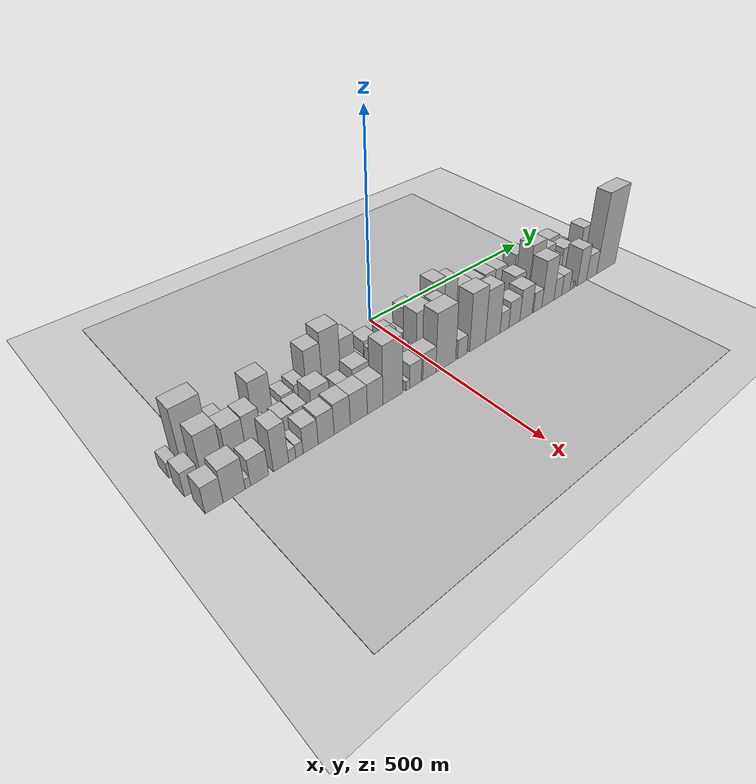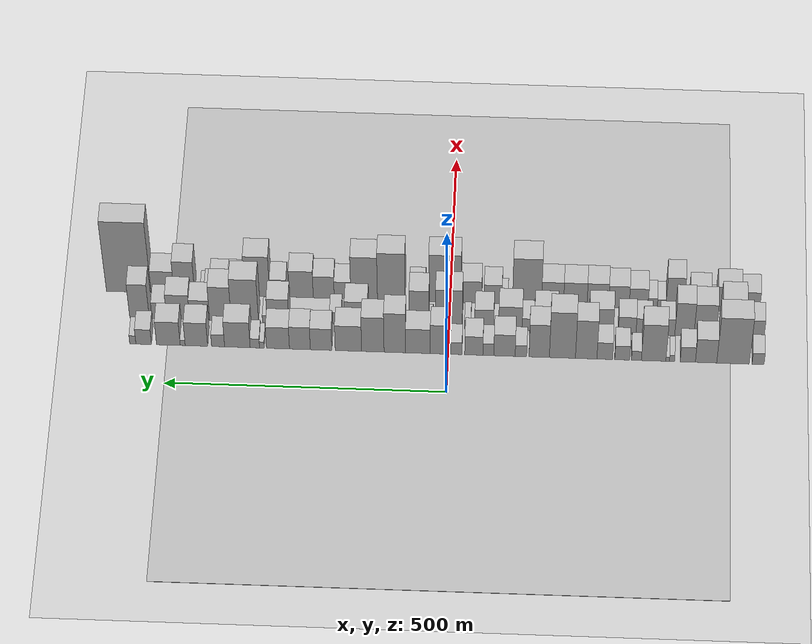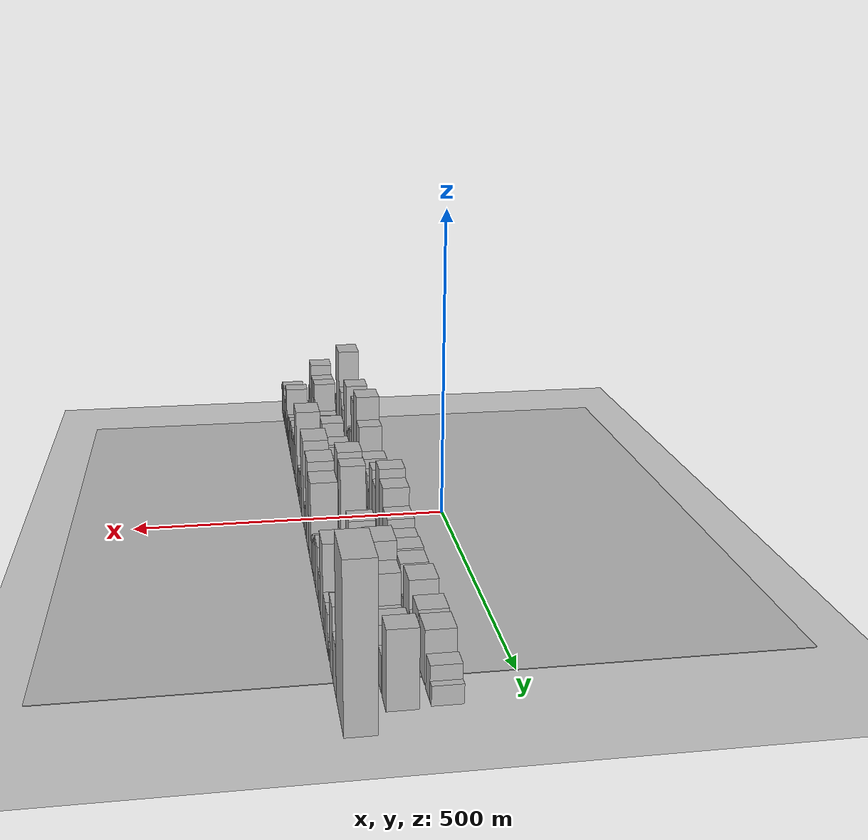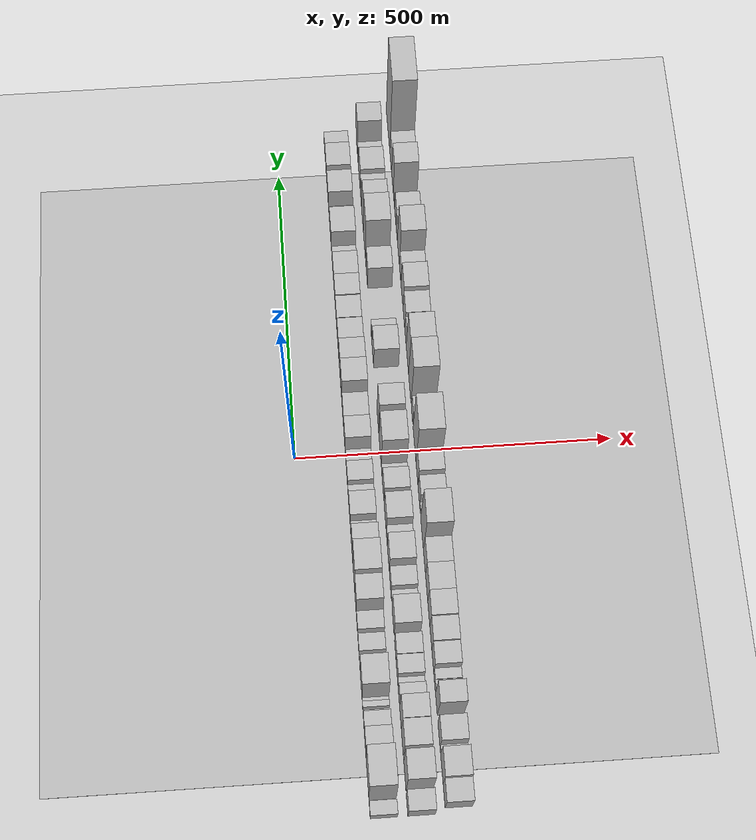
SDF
<?xml version="1.0" encoding="utf-8"?>

<sdf version="1.6">

   <world name="default">

      <gui fullscreen="0">

         <camera name="user_camera">

            <pose>-15 0 4.57585 0 0 0</pose>

            <view_controller>orbit</view_controller>

         </camera>

      </gui>

      <scene>

         <sky>

           <clouds>

             <speed>12</speed>

           </clouds>

         </sky>

         <ambient>0.4 0.4 0.4 1</ambient>

         <background>0.7 0.7 0.7 1</background>

         <shadows>1</shadows>

      </scene>

      <gravity>0 0 -9.8066</gravity>

      <magnetic_field>6e-06 2.3e-05 -4.2e-05</magnetic_field>

      <physics default="0" name="default_physics" type="ode">

         <ode>

            <solver>

               <type>quick</type>

               <iters>10</iters>

               <sor>1.0</sor>

               <use_dynamic_moi_rescaling>0</use_dynamic_moi_rescaling>

            </solver>

            <constraints>

               <cfm>0</cfm>

               <erp>0.2</erp>

               <contact_max_correcting_vel>100</contact_max_correcting_vel>

               <contact_surface_layer>0.001</contact_surface_layer>

            </constraints>

         </ode>

         <max_step_size>0.004</max_step_size>

         <real_time_factor>1</real_time_factor>

         <real_time_update_rate>250</real_time_update_rate>

      </physics>

      <light name="sun" type="directional">

         <cast_shadows>1</cast_shadows>

         <pose>0 0 10 0 0 0</pose>

         <diffuse>0.8 0.8 0.8 1</diffuse>

         <specular>0.2 0.2 0.2 1</specular>

         <attenuation>

            <range>1000</range>

            <constant>0.9</constant>

            <linear>0.01</linear>

            <quadratic>0.001</quadratic>

         </attenuation>

         <direction>-0.5 0.1 -0.9</direction>

      </light>

      <include>

         <name>ground_plane_1</name>

         <uri>model://HANNAS_ground_plane</uri>

         <pose>0 0 0  0 0 0</pose>

      </include>

      <include>

         <name>ground_plane_2</name>

         <uri>model://HANNAS_ground_plane</uri>

         <pose>100 0 0  0 0 0</pose>

      </include>

      <model name="building_1">

         <static>1</static>

         <pose frame="">100.0000 -549.3351 0 0.000000 0.000000 0.000000</pose>

         <link name="link">

            <pose frame="">0 0 18.00 0 0 0</pose>

            <collision name="collision">

               <geometry>

                  <box>

                     <size>40.0000 21.3298 36.0000</size>

                  </box>

               </geometry>

               <max_contacts>10</max_contacts>

               <surface>

                  <contact>

                     <ode/>

                  </contact>

                  <bounce/>

                  <friction>

                     <torsional>

                        <ode/>

                     </torsional>

                     <ode/>

                  </friction>

               </surface>

            </collision>

            <visual name="visual">

               <cast_shadows>0</cast_shadows>

               <geometry>

                  <box>

                     <size>40.0000 21.3298 36.0000</size>

                  </box>

               </geometry>

               <material>

                  <script>

                     <uri>model://HANNAS_wall/materials/scripts</uri>

                     <uri>model://HANNAS_wall/materials/textures</uri>

                     <name>vrc/HANNAS_wall</name>

                  </script>

               </material>

            </visual>

            <self_collide>0</self_collide>

            <enable_wind>0</enable_wind>

            <kinematic>0</kinematic>

         </link>

      </model>

      <model name="building_2">

         <static>1</static>

         <pose frame="">100.0000 -504.9209 0 0.000000 0.000000 0.000000</pose>

         <link name="link">

            <pose frame="">0 0 73.50 0 0 0</pose>

            <collision name="collision">

               <geometry>

                  <box>

                     <size>40.0000 57.4987 147.0000</size>

                  </box>

               </geometry>

               <max_contacts>10</max_contacts>

               <surface>

                  <contact>

                     <ode/>

                  </contact>

                  <bounce/>

                  <friction>

                     <torsional>

                        <ode/>

                     </torsional>

                     <ode/>

                  </friction>

               </surface>

            </collision>

            <visual name="visual">

               <cast_shadows>0</cast_shadows>

               <geometry>

                  <box>

                     <size>40.0000 57.4987 147.0000</size>

                  </box>

               </geometry>

               <material>

                  <script>

                     <uri>model://HANNAS_wall/materials/scripts</uri>

                     <uri>model://HANNAS_wall/materials/textures</uri>

                     <name>vrc/HANNAS_wall</name>

                  </script>

               </material>

            </visual>

            <self_collide>0</self_collide>

            <enable_wind>0</enable_wind>

            <kinematic>0</kinematic>

         </link>

      </model>

      <model name="building_3">

         <static>1</static>

         <pose frame="">100.0000 -457.2303 0 0.000000 0.000000 0.000000</pose>

         <link name="link">

            <pose frame="">0 0 37.50 0 0 0</pose>

            <collision name="collision">

               <geometry>

                  <box>

                     <size>40.0000 37.8825 75.0000</size>

                  </box>

               </geometry>

               <max_contacts>10</max_contacts>

               <surface>

                  <contact>

                     <ode/>

                  </contact>

                  <bounce/>

                  <friction>

                     <torsional>

                        <ode/>

                     </torsional>

                     <ode/>

                  </friction>

               </surface>

            </collision>

            <visual name="visual">

               <cast_shadows>0</cast_shadows>

               <geometry>

                  <box>

                     <size>40.0000 37.8825 75.0000</size>

                  </box>

               </geometry>

               <material>

                  <script>

                     <uri>model://HANNAS_wall/materials/scripts</uri>

                     <uri>model://HANNAS_wall/materials/textures</uri>

                     <name>vrc/HANNAS_wall</name>

                  </script>

               </material>

            </visual>

            <self_collide>0</self_collide>

            <enable_wind>0</enable_wind>

            <kinematic>0</kinematic>

         </link>

      </model>

      <model name="building_4">

         <static>1</static>

         <pose frame="">100.0000 -424.8399 0 0.000000 0.000000 0.000000</pose>

         <link name="link">

            <pose frame="">0 0 24.00 0 0 0</pose>

            <collision name="collision">

               <geometry>

                  <box>

                     <size>40.0000 26.8981 48.0000</size>

                  </box>

               </geometry>

               <max_contacts>10</max_contacts>

               <surface>

                  <contact>

                     <ode/>

                  </contact>

                  <bounce/>

                  <friction>

                     <torsional>

                        <ode/>

                     </torsional>

                     <ode/>

                  </friction>

               </surface>

            </collision>

            <visual name="visual">

               <cast_shadows>0</cast_shadows>

               <geometry>

                  <box>

                     <size>40.0000 26.8981 48.0000</size>

                  </box>

               </geometry>

               <material>

                  <script>

                     <uri>model://HANNAS_wall/materials/scripts</uri>

                     <uri>model://HANNAS_wall/materials/textures</uri>

                     <name>vrc/HANNAS_wall</name>

                  </script>

               </material>

            </visual>

            <self_collide>0</self_collide>

            <enable_wind>0</enable_wind>

            <kinematic>0</kinematic>

         </link>

      </model>

      <model name="building_5">

         <static>1</static>

         <pose frame="">100.0000 -396.7720 0 0.000000 0.000000 0.000000</pose>

         <link name="link">

            <pose frame="">0 0 10.50 0 0 0</pose>

            <collision name="collision">

               <geometry>

                  <box>

                     <size>40.0000 9.2377 21.0000</size>

                  </box>

               </geometry>

               <max_contacts>10</max_contacts>

               <surface>

                  <contact>

                     <ode/>

                  </contact>

                  <bounce/>

                  <friction>

                     <torsional>

                        <ode/>

                     </torsional>

                     <ode/>

                  </friction>

               </surface>

            </collision>

            <visual name="visual">

               <cast_shadows>0</cast_shadows>

               <geometry>

                  <box>

                     <size>40.0000 9.2377 21.0000</size>

                  </box>

               </geometry>

               <material>

                  <script>

                     <uri>model://HANNAS_wall/materials/scripts</uri>

                     <uri>model://HANNAS_wall/materials/textures</uri>

                     <name>vrc/HANNAS_wall</name>

                  </script>

               </material>

            </visual>

            <self_collide>0</self_collide>

            <enable_wind>0</enable_wind>

            <kinematic>0</kinematic>

         </link>

      </model>

      <model name="building_6">

         <static>1</static>

         <pose frame="">100.0000 -389.0437 0 0.000000 0.000000 0.000000</pose>

         <link name="link">

            <pose frame="">0 0 7.50 0 0 0</pose>

            <collision name="collision">

               <geometry>

                  <box>

                     <size>40.0000 6.2190 15.0000</size>

                  </box>

               </geometry>

               <max_contacts>10</max_contacts>

               <surface>

                  <contact>

                     <ode/>

                  </contact>

                  <bounce/>

                  <friction>

                     <torsional>

                        <ode/>

                     </torsional>

                     <ode/>

                  </friction>

               </surface>

            </collision>

            <visual name="visual">

               <cast_shadows>0</cast_shadows>

               <geometry>

                  <box>

                     <size>40.0000 6.2190 15.0000</size>

                  </box>

               </geometry>

               <material>

                  <script>

                     <uri>model://HANNAS_wall/materials/scripts</uri>

                     <uri>model://HANNAS_wall/materials/textures</uri>

                     <name>vrc/HANNAS_wall</name>

                  </script>

               </material>

            </visual>

            <self_collide>0</self_collide>

            <enable_wind>0</enable_wind>

            <kinematic>0</kinematic>

         </link>

      </model>

      <model name="building_7">

         <static>1</static>

         <pose frame="">100.0000 -364.2086 0 0.000000 0.000000 0.000000</pose>

         <link name="link">

            <pose frame="">0 0 58.50 0 0 0</pose>

            <collision name="collision">

               <geometry>

                  <box>

                     <size>40.0000 43.4513 117.0000</size>

                  </box>

               </geometry>

               <max_contacts>10</max_contacts>

               <surface>

                  <contact>

                     <ode/>

                  </contact>

                  <bounce/>

                  <friction>

                     <torsional>

                        <ode/>

                     </torsional>

                     <ode/>

                  </friction>

               </surface>

            </collision>

            <visual name="visual">

               <cast_shadows>0</cast_shadows>

               <geometry>

                  <box>

                     <size>40.0000 43.4513 117.0000</size>

                  </box>

               </geometry>

               <material>

                  <script>

                     <uri>model://HANNAS_wall/materials/scripts</uri>

                     <uri>model://HANNAS_wall/materials/textures</uri>

                     <name>vrc/HANNAS_wall</name>

                  </script>

               </material>

            </visual>

            <self_collide>0</self_collide>

            <enable_wind>0</enable_wind>

            <kinematic>0</kinematic>

         </link>

      </model>

      <model name="building_8">

         <static>1</static>

         <pose frame="">100.0000 -333.7156 0 0.000000 0.000000 0.000000</pose>

         <link name="link">

            <pose frame="">0 0 15.00 0 0 0</pose>

            <collision name="collision">

               <geometry>

                  <box>

                     <size>40.0000 17.5347 30.0000</size>

                  </box>

               </geometry>

               <max_contacts>10</max_contacts>

               <surface>

                  <contact>

                     <ode/>

                  </contact>

                  <bounce/>

                  <friction>

                     <torsional>

                        <ode/>

                     </torsional>

                     <ode/>

                  </friction>

               </surface>

            </collision>

            <visual name="visual">

               <cast_shadows>0</cast_shadows>

               <geometry>

                  <box>

                     <size>40.0000 17.5347 30.0000</size>

                  </box>

               </geometry>

               <material>

                  <script>

                     <uri>model://HANNAS_wall/materials/scripts</uri>

                     <uri>model://HANNAS_wall/materials/textures</uri>

                     <name>vrc/HANNAS_wall</name>

                  </script>

               </material>

            </visual>

            <self_collide>0</self_collide>

            <enable_wind>0</enable_wind>

            <kinematic>0</kinematic>

         </link>

      </model>

      <model name="building_9">

         <static>1</static>

         <pose frame="">100.0000 -308.6687 0 0.000000 0.000000 0.000000</pose>

         <link name="link">

            <pose frame="">0 0 22.50 0 0 0</pose>

            <collision name="collision">

               <geometry>

                  <box>

                     <size>40.0000 26.5590 45.0000</size>

                  </box>

               </geometry>

               <max_contacts>10</max_contacts>

               <surface>

                  <contact>

                     <ode/>

                  </contact>

                  <bounce/>

                  <friction>

                     <torsional>

                        <ode/>

                     </torsional>

                     <ode/>

                  </friction>

               </surface>

            </collision>

            <visual name="visual">

               <cast_shadows>0</cast_shadows>

               <geometry>

                  <box>

                     <size>40.0000 26.5590 45.0000</size>

                  </box>

               </geometry>

               <material>

                  <script>

                     <uri>model://HANNAS_wall/materials/scripts</uri>

                     <uri>model://HANNAS_wall/materials/textures</uri>

                     <name>vrc/HANNAS_wall</name>

                  </script>

               </material>

            </visual>

            <self_collide>0</self_collide>

            <enable_wind>0</enable_wind>

            <kinematic>0</kinematic>

         </link>

      </model>

      <model name="building_10">

         <static>1</static>

         <pose frame="">100.0000 -277.5191 0 0.000000 0.000000 0.000000</pose>

         <link name="link">

            <pose frame="">0 0 27.00 0 0 0</pose>

            <collision name="collision">

               <geometry>

                  <box>

                     <size>40.0000 27.7403 54.0000</size>

                  </box>

               </geometry>

               <max_contacts>10</max_contacts>

               <surface>

                  <contact>

                     <ode/>

                  </contact>

                  <bounce/>

                  <friction>

                     <torsional>

                        <ode/>

                     </torsional>

                     <ode/>

                  </friction>

               </surface>

            </collision>

            <visual name="visual">

               <cast_shadows>0</cast_shadows>

               <geometry>

                  <box>

                     <size>40.0000 27.7403 54.0000</size>

                  </box>

               </geometry>

               <material>

                  <script>

                     <uri>model://HANNAS_wall/materials/scripts</uri>

                     <uri>model://HANNAS_wall/materials/textures</uri>

                     <name>vrc/HANNAS_wall</name>

                  </script>

               </material>

            </visual>

            <self_collide>0</self_collide>

            <enable_wind>0</enable_wind>

            <kinematic>0</kinematic>

         </link>

      </model>

      <model name="building_11">

         <static>1</static>

         <pose frame="">100.0000 -244.6015 0 0.000000 0.000000 0.000000</pose>

         <link name="link">

            <pose frame="">0 0 61.50 0 0 0</pose>

            <collision name="collision">

               <geometry>

                  <box>

                     <size>40.0000 38.0948 123.0000</size>

                  </box>

               </geometry>

               <max_contacts>10</max_contacts>

               <surface>

                  <contact>

                     <ode/>

                  </contact>

                  <bounce/>

                  <friction>

                     <torsional>

                        <ode/>

                     </torsional>

                     <ode/>

                  </friction>

               </surface>

            </collision>

            <visual name="visual">

               <cast_shadows>0</cast_shadows>

               <geometry>

                  <box>

                     <size>40.0000 38.0948 123.0000</size>

                  </box>

               </geometry>

               <material>

                  <script>

                     <uri>model://HANNAS_wall/materials/scripts</uri>

                     <uri>model://HANNAS_wall/materials/textures</uri>

                     <name>vrc/HANNAS_wall</name>

                  </script>

               </material>

            </visual>

            <self_collide>0</self_collide>

            <enable_wind>0</enable_wind>

            <kinematic>0</kinematic>

         </link>

      </model>

      <model name="building_12">

         <static>1</static>

         <pose frame="">100.0000 -202.4772 0 0.000000 0.000000 0.000000</pose>

         <link name="link">

            <pose frame="">0 0 73.50 0 0 0</pose>

            <collision name="collision">

               <geometry>

                  <box>

                     <size>40.0000 46.1538 147.0000</size>

                  </box>

               </geometry>

               <max_contacts>10</max_contacts>

               <surface>

                  <contact>

                     <ode/>

                  </contact>

                  <bounce/>

                  <friction>

                     <torsional>

                        <ode/>

                     </torsional>

                     <ode/>

                  </friction>

               </surface>

            </collision>

            <visual name="visual">

               <cast_shadows>0</cast_shadows>

               <geometry>

                  <box>

                     <size>40.0000 46.1538 147.0000</size>

                  </box>

               </geometry>

               <material>

                  <script>

                     <uri>model://HANNAS_wall/materials/scripts</uri>

                     <uri>model://HANNAS_wall/materials/textures</uri>

                     <name>vrc/HANNAS_wall</name>

                  </script>

               </material>

            </visual>

            <self_collide>0</self_collide>

            <enable_wind>0</enable_wind>

            <kinematic>0</kinematic>

         </link>

      </model>

      <model name="building_13">

         <static>1</static>

         <pose frame="">100.0000 -161.3145 0 0.000000 0.000000 0.000000</pose>

         <link name="link">

            <pose frame="">0 0 52.50 0 0 0</pose>

            <collision name="collision">

               <geometry>

                  <box>

                     <size>40.0000 36.1715 105.0000</size>

                  </box>

               </geometry>

               <max_contacts>10</max_contacts>

               <surface>

                  <contact>

                     <ode/>

                  </contact>

                  <bounce/>

                  <friction>

                     <torsional>

                        <ode/>

                     </torsional>

                     <ode/>

                  </friction>

               </surface>

            </collision>

            <visual name="visual">

               <cast_shadows>0</cast_shadows>

               <geometry>

                  <box>

                     <size>40.0000 36.1715 105.0000</size>

                  </box>

               </geometry>

               <material>

                  <script>

                     <uri>model://HANNAS_wall/materials/scripts</uri>

                     <uri>model://HANNAS_wall/materials/textures</uri>

                     <name>vrc/HANNAS_wall</name>

                  </script>

               </material>

            </visual>

            <self_collide>0</self_collide>

            <enable_wind>0</enable_wind>

            <kinematic>0</kinematic>

         </link>

      </model>

      <model name="building_14">

         <static>1</static>

         <pose frame="">100.0000 -128.9654 0 0.000000 0.000000 0.000000</pose>

         <link name="link">

            <pose frame="">0 0 18.00 0 0 0</pose>

            <collision name="collision">

               <geometry>

                  <box>

                     <size>40.0000 20.5266 36.0000</size>

                  </box>

               </geometry>

               <max_contacts>10</max_contacts>

               <surface>

                  <contact>

                     <ode/>

                  </contact>

                  <bounce/>

                  <friction>

                     <torsional>

                        <ode/>

                     </torsional>

                     <ode/>

                  </friction>

               </surface>

            </collision>

            <visual name="visual">

               <cast_shadows>0</cast_shadows>

               <geometry>

                  <box>

                     <size>40.0000 20.5266 36.0000</size>

                  </box>

               </geometry>

               <material>

                  <script>

                     <uri>model://HANNAS_wall/materials/scripts</uri>

                     <uri>model://HANNAS_wall/materials/textures</uri>

                     <name>vrc/HANNAS_wall</name>

                  </script>

               </material>

            </visual>

            <self_collide>0</self_collide>

            <enable_wind>0</enable_wind>

            <kinematic>0</kinematic>

         </link>

      </model>

      <model name="building_15">

         <static>1</static>

         <pose frame="">100.0000 -99.7631 0 0.000000 0.000000 0.000000</pose>

         <link name="link">

            <pose frame="">0 0 34.50 0 0 0</pose>

            <collision name="collision">

               <geometry>

                  <box>

                     <size>40.0000 37.8780 69.0000</size>

                  </box>

               </geometry>

               <max_contacts>10</max_contacts>

               <surface>

                  <contact>

                     <ode/>

                  </contact>

                  <bounce/>

                  <friction>

                     <torsional>

                        <ode/>

                     </torsional>

                     <ode/>

                  </friction>

               </surface>

            </collision>

            <visual name="visual">

               <cast_shadows>0</cast_shadows>

               <geometry>

                  <box>

                     <size>40.0000 37.8780 69.0000</size>

                  </box>

               </geometry>

               <material>

                  <script>

                     <uri>model://HANNAS_wall/materials/scripts</uri>

                     <uri>model://HANNAS_wall/materials/textures</uri>

                     <name>vrc/HANNAS_wall</name>

                  </script>

               </material>

            </visual>

            <self_collide>0</self_collide>

            <enable_wind>0</enable_wind>

            <kinematic>0</kinematic>

         </link>

      </model>

      <model name="building_16">

         <static>1</static>

         <pose frame="">100.0000 -71.0460 0 0.000000 0.000000 0.000000</pose>

         <link name="link">

            <pose frame="">0 0 19.50 0 0 0</pose>

            <collision name="collision">

               <geometry>

                  <box>

                     <size>40.0000 19.5564 39.0000</size>

                  </box>

               </geometry>

               <max_contacts>10</max_contacts>

               <surface>

                  <contact>

                     <ode/>

                  </contact>

                  <bounce/>

                  <friction>

                     <torsional>

                        <ode/>

                     </torsional>

                     <ode/>

                  </friction>

               </surface>

            </collision>

            <visual name="visual">

               <cast_shadows>0</cast_shadows>

               <geometry>

                  <box>

                     <size>40.0000 19.5564 39.0000</size>

                  </box>

               </geometry>

               <material>

                  <script>

                     <uri>model://HANNAS_wall/materials/scripts</uri>

                     <uri>model://HANNAS_wall/materials/textures</uri>

                     <name>vrc/HANNAS_wall</name>

                  </script>

               </material>

            </visual>

            <self_collide>0</self_collide>

            <enable_wind>0</enable_wind>

            <kinematic>0</kinematic>

         </link>

      </model>

      <model name="building_17">

         <static>1</static>

         <pose frame="">100.0000 -45.1761 0 0.000000 0.000000 0.000000</pose>

         <link name="link">

            <pose frame="">0 0 30.00 0 0 0</pose>

            <collision name="collision">

               <geometry>

                  <box>

                     <size>40.0000 32.1834 60.0000</size>

                  </box>

               </geometry>

               <max_contacts>10</max_contacts>

               <surface>

                  <contact>

                     <ode/>

                  </contact>

                  <bounce/>

                  <friction>

                     <torsional>

                        <ode/>

                     </torsional>

                     <ode/>

                  </friction>

               </surface>

            </collision>

            <visual name="visual">

               <cast_shadows>0</cast_shadows>

               <geometry>

                  <box>

                     <size>40.0000 32.1834 60.0000</size>

                  </box>

               </geometry>

               <material>

                  <script>

                     <uri>model://HANNAS_wall/materials/scripts</uri>

                     <uri>model://HANNAS_wall/materials/textures</uri>

                     <name>vrc/HANNAS_wall</name>

                  </script>

               </material>

            </visual>

            <self_collide>0</self_collide>

            <enable_wind>0</enable_wind>

            <kinematic>0</kinematic>

         </link>

      </model>

      <model name="building_18">

         <static>1</static>

         <pose frame="">100.0000 -13.8160 0 0.000000 0.000000 0.000000</pose>

         <link name="link">

            <pose frame="">0 0 19.50 0 0 0</pose>

            <collision name="collision">

               <geometry>

                  <box>

                     <size>40.0000 20.5366 39.0000</size>

                  </box>

               </geometry>

               <max_contacts>10</max_contacts>

               <surface>

                  <contact>

                     <ode/>

                  </contact>

                  <bounce/>

                  <friction>

                     <torsional>

                        <ode/>

                     </torsional>

                     <ode/>

                  </friction>

               </surface>

            </collision>

            <visual name="visual">

               <cast_shadows>0</cast_shadows>

               <geometry>

                  <box>

                     <size>40.0000 20.5366 39.0000</size>

                  </box>

               </geometry>

               <material>

                  <script>

                     <uri>model://HANNAS_wall/materials/scripts</uri>

                     <uri>model://HANNAS_wall/materials/textures</uri>

                     <name>vrc/HANNAS_wall</name>

                  </script>

               </material>

            </visual>

            <self_collide>0</self_collide>

            <enable_wind>0</enable_wind>

            <kinematic>0</kinematic>

         </link>

      </model>

      <model name="building_19">

         <static>1</static>

         <pose frame="">100.0000 14.2060 0 0.000000 0.000000 0.000000</pose>

         <link name="link">

            <pose frame="">0 0 46.50 0 0 0</pose>

            <collision name="collision">

               <geometry>

                  <box>

                     <size>40.0000 35.5074 93.0000</size>

                  </box>

               </geometry>

               <max_contacts>10</max_contacts>

               <surface>

                  <contact>

                     <ode/>

                  </contact>

                  <bounce/>

                  <friction>

                     <torsional>

                        <ode/>

                     </torsional>

                     <ode/>

                  </friction>

               </surface>

            </collision>

            <visual name="visual">

               <cast_shadows>0</cast_shadows>

               <geometry>

                  <box>

                     <size>40.0000 35.5074 93.0000</size>

                  </box>

               </geometry>

               <material>

                  <script>

                     <uri>model://HANNAS_wall/materials/scripts</uri>

                     <uri>model://HANNAS_wall/materials/textures</uri>

                     <name>vrc/HANNAS_wall</name>

                  </script>

               </material>

            </visual>

            <self_collide>0</self_collide>

            <enable_wind>0</enable_wind>

            <kinematic>0</kinematic>

         </link>

      </model>

      <model name="building_20">

         <static>1</static>

         <pose frame="">100.0000 53.9739 0 0.000000 0.000000 0.000000</pose>

         <link name="link">

            <pose frame="">0 0 39.00 0 0 0</pose>

            <collision name="collision">

               <geometry>

                  <box>

                     <size>40.0000 44.0286 78.0000</size>

                  </box>

               </geometry>

               <max_contacts>10</max_contacts>

               <surface>

                  <contact>

                     <ode/>

                  </contact>

                  <bounce/>

                  <friction>

                     <torsional>

                        <ode/>

                     </torsional>

                     <ode/>

                  </friction>

               </surface>

            </collision>

            <visual name="visual">

               <cast_shadows>0</cast_shadows>

               <geometry>

                  <box>

                     <size>40.0000 44.0286 78.0000</size>

                  </box>

               </geometry>

               <material>

                  <script>

                     <uri>model://HANNAS_wall/materials/scripts</uri>

                     <uri>model://HANNAS_wall/materials/textures</uri>

                     <name>vrc/HANNAS_wall</name>

                  </script>

               </material>

            </visual>

            <self_collide>0</self_collide>

            <enable_wind>0</enable_wind>

            <kinematic>0</kinematic>

         </link>

      </model>

      <model name="building_21">

         <static>1</static>

         <pose frame="">100.0000 95.1085 0 0.000000 0.000000 0.000000</pose>

         <link name="link">

            <pose frame="">0 0 63.00 0 0 0</pose>

            <collision name="collision">

               <geometry>

                  <box>

                     <size>40.0000 38.2406 126.0000</size>

                  </box>

               </geometry>

               <max_contacts>10</max_contacts>

               <surface>

                  <contact>

                     <ode/>

                  </contact>

                  <bounce/>

                  <friction>

                     <torsional>

                        <ode/>

                     </torsional>

                     <ode/>

                  </friction>

               </surface>

            </collision>

            <visual name="visual">

               <cast_shadows>0</cast_shadows>

               <geometry>

                  <box>

                     <size>40.0000 38.2406 126.0000</size>

                  </box>

               </geometry>

               <material>

                  <script>

                     <uri>model://HANNAS_wall/materials/scripts</uri>

                     <uri>model://HANNAS_wall/materials/textures</uri>

                     <name>vrc/HANNAS_wall</name>

                  </script>

               </material>

            </visual>

            <self_collide>0</self_collide>

            <enable_wind>0</enable_wind>

            <kinematic>0</kinematic>

         </link>

      </model>

      <model name="building_22">

         <static>1</static>

         <pose frame="">100.0000 134.1365 0 0.000000 0.000000 0.000000</pose>

         <link name="link">

            <pose frame="">0 0 55.50 0 0 0</pose>

            <collision name="collision">

               <geometry>

                  <box>

                     <size>40.0000 39.8153 111.0000</size>

                  </box>

               </geometry>

               <max_contacts>10</max_contacts>

               <surface>

                  <contact>

                     <ode/>

                  </contact>

                  <bounce/>

                  <friction>

                     <torsional>

                        <ode/>

                     </torsional>

                     <ode/>

                  </friction>

               </surface>

            </collision>

            <visual name="visual">

               <cast_shadows>0</cast_shadows>

               <geometry>

                  <box>

                     <size>40.0000 39.8153 111.0000</size>

                  </box>

               </geometry>

               <material>

                  <script>

                     <uri>model://HANNAS_wall/materials/scripts</uri>

                     <uri>model://HANNAS_wall/materials/textures</uri>

                     <name>vrc/HANNAS_wall</name>

                  </script>

               </material>

            </visual>

            <self_collide>0</self_collide>

            <enable_wind>0</enable_wind>

            <kinematic>0</kinematic>

         </link>

      </model>

      <model name="building_23">

         <static>1</static>

         <pose frame="">100.0000 177.5344 0 0.000000 0.000000 0.000000</pose>

         <link name="link">

            <pose frame="">0 0 40.50 0 0 0</pose>

            <collision name="collision">

               <geometry>

                  <box>

                     <size>40.0000 46.9805 81.0000</size>

                  </box>

               </geometry>

               <max_contacts>10</max_contacts>

               <surface>

                  <contact>

                     <ode/>

                  </contact>

                  <bounce/>

                  <friction>

                     <torsional>

                        <ode/>

                     </torsional>

                     <ode/>

                  </friction>

               </surface>

            </collision>

            <visual name="visual">

               <cast_shadows>0</cast_shadows>

               <geometry>

                  <box>

                     <size>40.0000 46.9805 81.0000</size>

                  </box>

               </geometry>

               <material>

                  <script>

                     <uri>model://HANNAS_wall/materials/scripts</uri>

                     <uri>model://HANNAS_wall/materials/textures</uri>

                     <name>vrc/HANNAS_wall</name>

                  </script>

               </material>

            </visual>

            <self_collide>0</self_collide>

            <enable_wind>0</enable_wind>

            <kinematic>0</kinematic>

         </link>

      </model>

      <model name="building_24">

         <static>1</static>

         <pose frame="">100.0000 226.1915 0 0.000000 0.000000 0.000000</pose>

         <link name="link">

            <pose frame="">0 0 34.50 0 0 0</pose>

            <collision name="collision">

               <geometry>

                  <box>

                     <size>40.0000 38.3338 69.0000</size>

                  </box>

               </geometry>

               <max_contacts>10</max_contacts>

               <surface>

                  <contact>

                     <ode/>

                  </contact>

                  <bounce/>

                  <friction>

                     <torsional>

                        <ode/>

                     </torsional>

                     <ode/>

                  </friction>

               </surface>

            </collision>

            <visual name="visual">

               <cast_shadows>0</cast_shadows>

               <geometry>

                  <box>

                     <size>40.0000 38.3338 69.0000</size>

                  </box>

               </geometry>

               <material>

                  <script>

                     <uri>model://HANNAS_wall/materials/scripts</uri>

                     <uri>model://HANNAS_wall/materials/textures</uri>

                     <name>vrc/HANNAS_wall</name>

                  </script>

               </material>

            </visual>

            <self_collide>0</self_collide>

            <enable_wind>0</enable_wind>

            <kinematic>0</kinematic>

         </link>

      </model>

      <model name="building_25">

         <static>1</static>

         <pose frame="">100.0000 263.8950 0 0.000000 0.000000 0.000000</pose>

         <link name="link">

            <pose frame="">0 0 36.00 0 0 0</pose>

            <collision name="collision">

               <geometry>

                  <box>

                     <size>40.0000 37.0732 72.0000</size>

                  </box>

               </geometry>

               <max_contacts>10</max_contacts>

               <surface>

                  <contact>

                     <ode/>

                  </contact>

                  <bounce/>

                  <friction>

                     <torsional>

                        <ode/>

                     </torsional>

                     <ode/>

                  </friction>

               </surface>

            </collision>

            <visual name="visual">

               <cast_shadows>0</cast_shadows>

               <geometry>

                  <box>

                     <size>40.0000 37.0732 72.0000</size>

                  </box>

               </geometry>

               <material>

                  <script>

                     <uri>model://HANNAS_wall/materials/scripts</uri>

                     <uri>model://HANNAS_wall/materials/textures</uri>

                     <name>vrc/HANNAS_wall</name>

                  </script>

               </material>

            </visual>

            <self_collide>0</self_collide>

            <enable_wind>0</enable_wind>

            <kinematic>0</kinematic>

         </link>

      </model>

      <model name="building_26">

         <static>1</static>

         <pose frame="">100.0000 302.8629 0 0.000000 0.000000 0.000000</pose>

         <link name="link">

            <pose frame="">0 0 34.50 0 0 0</pose>

            <collision name="collision">

               <geometry>

                  <box>

                     <size>40.0000 40.8625 69.0000</size>

                  </box>

               </geometry>

               <max_contacts>10</max_contacts>

               <surface>

                  <contact>

                     <ode/>

                  </contact>

                  <bounce/>

                  <friction>

                     <torsional>

                        <ode/>

                     </torsional>

                     <ode/>

                  </friction>

               </surface>

            </collision>

            <visual name="visual">

               <cast_shadows>0</cast_shadows>

               <geometry>

                  <box>

                     <size>40.0000 40.8625 69.0000</size>

                  </box>

               </geometry>

               <material>

                  <script>

                     <uri>model://HANNAS_wall/materials/scripts</uri>

                     <uri>model://HANNAS_wall/materials/textures</uri>

                     <name>vrc/HANNAS_wall</name>

                  </script>

               </material>

            </visual>

            <self_collide>0</self_collide>

            <enable_wind>0</enable_wind>

            <kinematic>0</kinematic>

         </link>

      </model>

      <model name="building_27">

         <static>1</static>

         <pose frame="">100.0000 331.5423 0 0.000000 0.000000 0.000000</pose>

         <link name="link">

            <pose frame="">0 0 10.50 0 0 0</pose>

            <collision name="collision">

               <geometry>

                  <box>

                     <size>40.0000 8.4963 21.0000</size>

                  </box>

               </geometry>

               <max_contacts>10</max_contacts>

               <surface>

                  <contact>

                     <ode/>

                  </contact>

                  <bounce/>

                  <friction>

                     <torsional>

                        <ode/>

                     </torsional>

                     <ode/>

                  </friction>

               </surface>

            </collision>

            <visual name="visual">

               <cast_shadows>0</cast_shadows>

               <geometry>

                  <box>

                     <size>40.0000 8.4963 21.0000</size>

                  </box>

               </geometry>

               <material>

                  <script>

                     <uri>model://HANNAS_wall/materials/scripts</uri>

                     <uri>model://HANNAS_wall/materials/textures</uri>

                     <name>vrc/HANNAS_wall</name>

                  </script>

               </material>

            </visual>

            <self_collide>0</self_collide>

            <enable_wind>0</enable_wind>

            <kinematic>0</kinematic>

         </link>

      </model>

      <model name="building_28">

         <static>1</static>

         <pose frame="">100.0000 344.0864 0 0.000000 0.000000 0.000000</pose>

         <link name="link">

            <pose frame="">0 0 15.00 0 0 0</pose>

            <collision name="collision">

               <geometry>

                  <box>

                     <size>40.0000 16.5918 30.0000</size>

                  </box>

               </geometry>

               <max_contacts>10</max_contacts>

               <surface>

                  <contact>

                     <ode/>

                  </contact>

                  <bounce/>

                  <friction>

                     <torsional>

                        <ode/>

                     </torsional>

                     <ode/>

                  </friction>

               </surface>

            </collision>

            <visual name="visual">

               <cast_shadows>0</cast_shadows>

               <geometry>

                  <box>

                     <size>40.0000 16.5918 30.0000</size>

                  </box>

               </geometry>

               <material>

                  <script>

                     <uri>model://HANNAS_wall/materials/scripts</uri>

                     <uri>model://HANNAS_wall/materials/textures</uri>

                     <name>vrc/HANNAS_wall</name>

                  </script>

               </material>

            </visual>

            <self_collide>0</self_collide>

            <enable_wind>0</enable_wind>

            <kinematic>0</kinematic>

         </link>

      </model>

      <model name="building_29">

         <static>1</static>

         <pose frame="">100.0000 375.1154 0 0.000000 0.000000 0.000000</pose>

         <link name="link">

            <pose frame="">0 0 40.50 0 0 0</pose>

            <collision name="collision">

               <geometry>

                  <box>

                     <size>40.0000 45.4663 81.0000</size>

                  </box>

               </geometry>

               <max_contacts>10</max_contacts>

               <surface>

                  <contact>

                     <ode/>

                  </contact>

                  <bounce/>

                  <friction>

                     <torsional>

                        <ode/>

                     </torsional>

                     <ode/>

                  </friction>

               </surface>

            </collision>

            <visual name="visual">

               <cast_shadows>0</cast_shadows>

               <geometry>

                  <box>

                     <size>40.0000 45.4663 81.0000</size>

                  </box>

               </geometry>

               <material>

                  <script>

                     <uri>model://HANNAS_wall/materials/scripts</uri>

                     <uri>model://HANNAS_wall/materials/textures</uri>

                     <name>vrc/HANNAS_wall</name>

                  </script>

               </material>

            </visual>

            <self_collide>0</self_collide>

            <enable_wind>0</enable_wind>

            <kinematic>0</kinematic>

         </link>

      </model>

      <model name="building_30">

         <static>1</static>

         <pose frame="">100.0000 409.4259 0 0.000000 0.000000 0.000000</pose>

         <link name="link">

            <pose frame="">0 0 19.50 0 0 0</pose>

            <collision name="collision">

               <geometry>

                  <box>

                     <size>40.0000 23.1548 39.0000</size>

                  </box>

               </geometry>

               <max_contacts>10</max_contacts>

               <surface>

                  <contact>

                     <ode/>

                  </contact>

                  <bounce/>

                  <friction>

                     <torsional>

                        <ode/>

                     </torsional>

                     <ode/>

                  </friction>

               </surface>

            </collision>

            <visual name="visual">

               <cast_shadows>0</cast_shadows>

               <geometry>

                  <box>

                     <size>40.0000 23.1548 39.0000</size>

                  </box>

               </geometry>

               <material>

                  <script>

                     <uri>model://HANNAS_wall/materials/scripts</uri>

                     <uri>model://HANNAS_wall/materials/textures</uri>

                     <name>vrc/HANNAS_wall</name>

                  </script>

               </material>

            </visual>

            <self_collide>0</self_collide>

            <enable_wind>0</enable_wind>

            <kinematic>0</kinematic>

         </link>

      </model>

      <model name="building_31">

         <static>1</static>

         <pose frame="">100.0000 448.0547 0 0.000000 0.000000 0.000000</pose>

         <link name="link">

            <pose frame="">0 0 37.50 0 0 0</pose>

            <collision name="collision">

               <geometry>

                  <box>

                     <size>40.0000 40.1027 75.0000</size>

                  </box>

               </geometry>

               <max_contacts>10</max_contacts>

               <surface>

                  <contact>

                     <ode/>

                  </contact>

                  <bounce/>

                  <friction>

                     <torsional>

                        <ode/>

                     </torsional>

                     <ode/>

                  </friction>

               </surface>

            </collision>

            <visual name="visual">

               <cast_shadows>0</cast_shadows>

               <geometry>

                  <box>

                     <size>40.0000 40.1027 75.0000</size>

                  </box>

               </geometry>

               <material>

                  <script>

                     <uri>model://HANNAS_wall/materials/scripts</uri>

                     <uri>model://HANNAS_wall/materials/textures</uri>

                     <name>vrc/HANNAS_wall</name>

                  </script>

               </material>

            </visual>

            <self_collide>0</self_collide>

            <enable_wind>0</enable_wind>

            <kinematic>0</kinematic>

         </link>

      </model>

      <model name="building_32">

         <static>1</static>

         <pose frame="">100.0000 472.4805 0 0.000000 0.000000 0.000000</pose>

         <link name="link">

            <pose frame="">0 0 9.00 0 0 0</pose>

            <collision name="collision">

               <geometry>

                  <box>

                     <size>40.0000 8.7489 18.0000</size>

                  </box>

               </geometry>

               <max_contacts>10</max_contacts>

               <surface>

                  <contact>

                     <ode/>

                  </contact>

                  <bounce/>

                  <friction>

                     <torsional>

                        <ode/>

                     </torsional>

                     <ode/>

                  </friction>

               </surface>

            </collision>

            <visual name="visual">

               <cast_shadows>0</cast_shadows>

               <geometry>

                  <box>

                     <size>40.0000 8.7489 18.0000</size>

                  </box>

               </geometry>

               <material>

                  <script>

                     <uri>model://HANNAS_wall/materials/scripts</uri>

                     <uri>model://HANNAS_wall/materials/textures</uri>

                     <name>vrc/HANNAS_wall</name>

                  </script>

               </material>

            </visual>

            <self_collide>0</self_collide>

            <enable_wind>0</enable_wind>

            <kinematic>0</kinematic>

         </link>

      </model>

      <model name="building_33">

         <static>1</static>

         <pose frame="">100.0000 497.9896 0 0.000000 0.000000 0.000000</pose>

         <link name="link">

            <pose frame="">0 0 37.50 0 0 0</pose>

            <collision name="collision">

               <geometry>

                  <box>

                     <size>40.0000 42.2691 75.0000</size>

                  </box>

               </geometry>

               <max_contacts>10</max_contacts>

               <surface>

                  <contact>

                     <ode/>

                  </contact>

                  <bounce/>

                  <friction>

                     <torsional>

                        <ode/>

                     </torsional>

                     <ode/>

                  </friction>

               </surface>

            </collision>

            <visual name="visual">

               <cast_shadows>0</cast_shadows>

               <geometry>

                  <box>

                     <size>40.0000 42.2691 75.0000</size>

                  </box>

               </geometry>

               <material>

                  <script>

                     <uri>model://HANNAS_wall/materials/scripts</uri>

                     <uri>model://HANNAS_wall/materials/textures</uri>

                     <name>vrc/HANNAS_wall</name>

                  </script>

               </material>

            </visual>

            <self_collide>0</self_collide>

            <enable_wind>0</enable_wind>

            <kinematic>0</kinematic>

         </link>

      </model>

      <model name="building_34">

         <static>1</static>

         <pose frame="">100.0000 542.0247 0 0.000000 0.000000 0.000000</pose>

         <link name="link">

            <pose frame="">0 0 24.00 0 0 0</pose>

            <collision name="collision">

               <geometry>

                  <box>

                     <size>40.0000 27.8012 48.0000</size>

                  </box>

               </geometry>

               <max_contacts>10</max_contacts>

               <surface>

                  <contact>

                     <ode/>

                  </contact>

                  <bounce/>

                  <friction>

                     <torsional>

                        <ode/>

                     </torsional>

                     <ode/>

                  </friction>

               </surface>

            </collision>

            <visual name="visual">

               <cast_shadows>0</cast_shadows>

               <geometry>

                  <box>

                     <size>40.0000 27.8012 48.0000</size>

                  </box>

               </geometry>

               <material>

                  <script>

                     <uri>model://HANNAS_wall/materials/scripts</uri>

                     <uri>model://HANNAS_wall/materials/textures</uri>

                     <name>vrc/HANNAS_wall</name>

                  </script>

               </material>

            </visual>

            <self_collide>0</self_collide>

            <enable_wind>0</enable_wind>

            <kinematic>0</kinematic>

         </link>

      </model>

      <model name="building_35">

         <static>1</static>

         <pose frame="">100.0000 561.4147 0 0.000000 0.000000 0.000000</pose>

         <link name="link">

            <pose frame="">0 0 13.50 0 0 0</pose>

            <collision name="collision">

               <geometry>

                  <box>

                     <size>40.0000 10.9788 27.0000</size>

                  </box>

               </geometry>

               <max_contacts>10</max_contacts>

               <surface>

                  <contact>

                     <ode/>

                  </contact>

                  <bounce/>

                  <friction>

                     <torsional>

                        <ode/>

                     </torsional>

                     <ode/>

                  </friction>

               </surface>

            </collision>

            <visual name="visual">

               <cast_shadows>0</cast_shadows>

               <geometry>

                  <box>

                     <size>40.0000 10.9788 27.0000</size>

                  </box>

               </geometry>

               <material>

                  <script>

                     <uri>model://HANNAS_wall/materials/scripts</uri>

                     <uri>model://HANNAS_wall/materials/textures</uri>

                     <name>vrc/HANNAS_wall</name>

                  </script>

               </material>

            </visual>

            <self_collide>0</self_collide>

            <enable_wind>0</enable_wind>

            <kinematic>0</kinematic>

         </link>

      </model>

      <model name="building_36">

         <static>1</static>

         <pose frame="">155.0000 -544.5624 0 0.000000 0.000000 0.000000</pose>

         <link name="link">

            <pose frame="">0 0 28.50 0 0 0</pose>

            <collision name="collision">

               <geometry>

                  <box>

                     <size>40.0000 30.8753 57.0000</size>

                  </box>

               </geometry>

               <max_contacts>10</max_contacts>

               <surface>

                  <contact>

                     <ode/>

                  </contact>

                  <bounce/>

                  <friction>

                     <torsional>

                        <ode/>

                     </torsional>

                     <ode/>

                  </friction>

               </surface>

            </collision>

            <visual name="visual">

               <cast_shadows>0</cast_shadows>

               <geometry>

                  <box>

                     <size>40.0000 30.8753 57.0000</size>

                  </box>

               </geometry>

               <material>

                  <script>

                     <uri>model://HANNAS_wall/materials/scripts</uri>

                     <uri>model://HANNAS_wall/materials/textures</uri>

                     <name>vrc/HANNAS_wall</name>

                  </script>

               </material>

            </visual>

            <self_collide>0</self_collide>

            <enable_wind>0</enable_wind>

            <kinematic>0</kinematic>

         </link>

      </model>

      <model name="building_37">

         <static>1</static>

         <pose frame="">155.0000 -502.6517 0 0.000000 0.000000 0.000000</pose>

         <link name="link">

            <pose frame="">0 0 60.00 0 0 0</pose>

            <collision name="collision">

               <geometry>

                  <box>

                     <size>40.0000 42.9461 120.0000</size>

                  </box>

               </geometry>

               <max_contacts>10</max_contacts>

               <surface>

                  <contact>

                     <ode/>

                  </contact>

                  <bounce/>

                  <friction>

                     <torsional>

                        <ode/>

                     </torsional>

                     <ode/>

                  </friction>

               </surface>

            </collision>

            <visual name="visual">

               <cast_shadows>0</cast_shadows>

               <geometry>

                  <box>

                     <size>40.0000 42.9461 120.0000</size>

                  </box>

               </geometry>

               <material>

                  <script>

                     <uri>model://HANNAS_wall/materials/scripts</uri>

                     <uri>model://HANNAS_wall/materials/textures</uri>

                     <name>vrc/HANNAS_wall</name>

                  </script>

               </material>

            </visual>

            <self_collide>0</self_collide>

            <enable_wind>0</enable_wind>

            <kinematic>0</kinematic>

         </link>

      </model>

      <model name="building_38">

         <static>1</static>

         <pose frame="">155.0000 -477.8783 0 0.000000 0.000000 0.000000</pose>

         <link name="link">

            <pose frame="">0 0 7.50 0 0 0</pose>

            <collision name="collision">

               <geometry>

                  <box>

                     <size>40.0000 6.6005 15.0000</size>

                  </box>

               </geometry>

               <max_contacts>10</max_contacts>

               <surface>

                  <contact>

                     <ode/>

                  </contact>

                  <bounce/>

                  <friction>

                     <torsional>

                        <ode/>

                     </torsional>

                     <ode/>

                  </friction>

               </surface>

            </collision>

            <visual name="visual">

               <cast_shadows>0</cast_shadows>

               <geometry>

                  <box>

                     <size>40.0000 6.6005 15.0000</size>

                  </box>

               </geometry>

               <material>

                  <script>

                     <uri>model://HANNAS_wall/materials/scripts</uri>

                     <uri>model://HANNAS_wall/materials/textures</uri>

                     <name>vrc/HANNAS_wall</name>

                  </script>

               </material>

            </visual>

            <self_collide>0</self_collide>

            <enable_wind>0</enable_wind>

            <kinematic>0</kinematic>

         </link>

      </model>

      <model name="building_39">

         <static>1</static>

         <pose frame="">155.0000 -454.9827 0 0.000000 0.000000 0.000000</pose>

         <link name="link">

            <pose frame="">0 0 51.00 0 0 0</pose>

            <collision name="collision">

               <geometry>

                  <box>

                     <size>40.0000 39.1908 102.0000</size>

                  </box>

               </geometry>

               <max_contacts>10</max_contacts>

               <surface>

                  <contact>

                     <ode/>

                  </contact>

                  <bounce/>

                  <friction>

                     <torsional>

                        <ode/>

                     </torsional>

                     <ode/>

                  </friction>

               </surface>

            </collision>

            <visual name="visual">

               <cast_shadows>0</cast_shadows>

               <geometry>

                  <box>

                     <size>40.0000 39.1908 102.0000</size>

                  </box>

               </geometry>

               <material>

                  <script>

                     <uri>model://HANNAS_wall/materials/scripts</uri>

                     <uri>model://HANNAS_wall/materials/textures</uri>

                     <name>vrc/HANNAS_wall</name>

                  </script>

               </material>

            </visual>

            <self_collide>0</self_collide>

            <enable_wind>0</enable_wind>

            <kinematic>0</kinematic>

         </link>

      </model>

      <model name="building_40">

         <static>1</static>

         <pose frame="">155.0000 -418.3287 0 0.000000 0.000000 0.000000</pose>

         <link name="link">

            <pose frame="">0 0 52.50 0 0 0</pose>

            <collision name="collision">

               <geometry>

                  <box>

                     <size>40.0000 34.1171 105.0000</size>

                  </box>

               </geometry>

               <max_contacts>10</max_contacts>

               <surface>

                  <contact>

                     <ode/>

                  </contact>

                  <bounce/>

                  <friction>

                     <torsional>

                        <ode/>

                     </torsional>

                     <ode/>

                  </friction>

               </surface>

            </collision>

            <visual name="visual">

               <cast_shadows>0</cast_shadows>

               <geometry>

                  <box>

                     <size>40.0000 34.1171 105.0000</size>

                  </box>

               </geometry>

               <material>

                  <script>

                     <uri>model://HANNAS_wall/materials/scripts</uri>

                     <uri>model://HANNAS_wall/materials/textures</uri>

                     <name>vrc/HANNAS_wall</name>

                  </script>

               </material>

            </visual>

            <self_collide>0</self_collide>

            <enable_wind>0</enable_wind>

            <kinematic>0</kinematic>

         </link>

      </model>

      <model name="building_41">

         <static>1</static>

         <pose frame="">155.0000 -387.9617 0 0.000000 0.000000 0.000000</pose>

         <link name="link">

            <pose frame="">0 0 25.50 0 0 0</pose>

            <collision name="collision">

               <geometry>

                  <box>

                     <size>40.0000 26.6170 51.0000</size>

                  </box>

               </geometry>

               <max_contacts>10</max_contacts>

               <surface>

                  <contact>

                     <ode/>

                  </contact>

                  <bounce/>

                  <friction>

                     <torsional>

                        <ode/>

                     </torsional>

                     <ode/>

                  </friction>

               </surface>

            </collision>

            <visual name="visual">

               <cast_shadows>0</cast_shadows>

               <geometry>

                  <box>

                     <size>40.0000 26.6170 51.0000</size>

                  </box>

               </geometry>

               <material>

                  <script>

                     <uri>model://HANNAS_wall/materials/scripts</uri>

                     <uri>model://HANNAS_wall/materials/textures</uri>

                     <name>vrc/HANNAS_wall</name>

                  </script>

               </material>

            </visual>

            <self_collide>0</self_collide>

            <enable_wind>0</enable_wind>

            <kinematic>0</kinematic>

         </link>

      </model>

      <model name="building_42">

         <static>1</static>

         <pose frame="">155.0000 -366.2097 0 0.000000 0.000000 0.000000</pose>

         <link name="link">

            <pose frame="">0 0 12.00 0 0 0</pose>

            <collision name="collision">

               <geometry>

                  <box>

                     <size>40.0000 10.8868 24.0000</size>

                  </box>

               </geometry>

               <max_contacts>10</max_contacts>

               <surface>

                  <contact>

                     <ode/>

                  </contact>

                  <bounce/>

                  <friction>

                     <torsional>

                        <ode/>

                     </torsional>

                     <ode/>

                  </friction>

               </surface>

            </collision>

            <visual name="visual">

               <cast_shadows>0</cast_shadows>

               <geometry>

                  <box>

                     <size>40.0000 10.8868 24.0000</size>

                  </box>

               </geometry>

               <material>

                  <script>

                     <uri>model://HANNAS_wall/materials/scripts</uri>

                     <uri>model://HANNAS_wall/materials/textures</uri>

                     <name>vrc/HANNAS_wall</name>

                  </script>

               </material>

            </visual>

            <self_collide>0</self_collide>

            <enable_wind>0</enable_wind>

            <kinematic>0</kinematic>

         </link>

      </model>

      <model name="building_43">

         <static>1</static>

         <pose frame="">155.0000 -346.4759 0 0.000000 0.000000 0.000000</pose>

         <link name="link">

            <pose frame="">0 0 25.50 0 0 0</pose>

            <collision name="collision">

               <geometry>

                  <box>

                     <size>40.0000 28.5809 51.0000</size>

                  </box>

               </geometry>

               <max_contacts>10</max_contacts>

               <surface>

                  <contact>

                     <ode/>

                  </contact>

                  <bounce/>

                  <friction>

                     <torsional>

                        <ode/>

                     </torsional>

                     <ode/>

                  </friction>

               </surface>

            </collision>

            <visual name="visual">

               <cast_shadows>0</cast_shadows>

               <geometry>

                  <box>

                     <size>40.0000 28.5809 51.0000</size>

                  </box>

               </geometry>

               <material>

                  <script>

                     <uri>model://HANNAS_wall/materials/scripts</uri>

                     <uri>model://HANNAS_wall/materials/textures</uri>

                     <name>vrc/HANNAS_wall</name>

                  </script>

               </material>

            </visual>

            <self_collide>0</self_collide>

            <enable_wind>0</enable_wind>

            <kinematic>0</kinematic>

         </link>

      </model>

      <model name="building_44">

         <static>1</static>

         <pose frame="">155.0000 -316.4502 0 0.000000 0.000000 0.000000</pose>

         <link name="link">

            <pose frame="">0 0 27.00 0 0 0</pose>

            <collision name="collision">

               <geometry>

                  <box>

                     <size>40.0000 31.4704 54.0000</size>

                  </box>

               </geometry>

               <max_contacts>10</max_contacts>

               <surface>

                  <contact>

                     <ode/>

                  </contact>

                  <bounce/>

                  <friction>

                     <torsional>

                        <ode/>

                     </torsional>

                     <ode/>

                  </friction>

               </surface>

            </collision>

            <visual name="visual">

               <cast_shadows>0</cast_shadows>

               <geometry>

                  <box>

                     <size>40.0000 31.4704 54.0000</size>

                  </box>

               </geometry>

               <material>

                  <script>

                     <uri>model://HANNAS_wall/materials/scripts</uri>

                     <uri>model://HANNAS_wall/materials/textures</uri>

                     <name>vrc/HANNAS_wall</name>

                  </script>

               </material>

            </visual>

            <self_collide>0</self_collide>

            <enable_wind>0</enable_wind>

            <kinematic>0</kinematic>

         </link>

      </model>

      <model name="building_45">

         <static>1</static>

         <pose frame="">155.0000 -270.0742 0 0.000000 0.000000 0.000000</pose>

         <link name="link">

            <pose frame="">0 0 39.00 0 0 0</pose>

            <collision name="collision">

               <geometry>

                  <box>

                     <size>40.0000 43.2818 78.0000</size>

                  </box>

               </geometry>

               <max_contacts>10</max_contacts>

               <surface>

                  <contact>

                     <ode/>

                  </contact>

                  <bounce/>

                  <friction>

                     <torsional>

                        <ode/>

                     </torsional>

                     <ode/>

                  </friction>

               </surface>

            </collision>

            <visual name="visual">

               <cast_shadows>0</cast_shadows>

               <geometry>

                  <box>

                     <size>40.0000 43.2818 78.0000</size>

                  </box>

               </geometry>

               <material>

                  <script>

                     <uri>model://HANNAS_wall/materials/scripts</uri>

                     <uri>model://HANNAS_wall/materials/textures</uri>

                     <name>vrc/HANNAS_wall</name>

                  </script>

               </material>

            </visual>

            <self_collide>0</self_collide>

            <enable_wind>0</enable_wind>

            <kinematic>0</kinematic>

         </link>

      </model>

      <model name="building_46">

         <static>1</static>

         <pose frame="">155.0000 -233.7053 0 0.000000 0.000000 0.000000</pose>

         <link name="link">

            <pose frame="">0 0 13.50 0 0 0</pose>

            <collision name="collision">

               <geometry>

                  <box>

                     <size>40.0000 11.4559 27.0000</size>

                  </box>

               </geometry>

               <max_contacts>10</max_contacts>

               <surface>

                  <contact>

                     <ode/>

                  </contact>

                  <bounce/>

                  <friction>

                     <torsional>

                        <ode/>

                     </torsional>

                     <ode/>

                  </friction>

               </surface>

            </collision>

            <visual name="visual">

               <cast_shadows>0</cast_shadows>

               <geometry>

                  <box>

                     <size>40.0000 11.4559 27.0000</size>

                  </box>

               </geometry>

               <material>

                  <script>

                     <uri>model://HANNAS_wall/materials/scripts</uri>

                     <uri>model://HANNAS_wall/materials/textures</uri>

                     <name>vrc/HANNAS_wall</name>

                  </script>

               </material>

            </visual>

            <self_collide>0</self_collide>

            <enable_wind>0</enable_wind>

            <kinematic>0</kinematic>

         </link>

      </model>

      <model name="building_47">

         <static>1</static>

         <pose frame="">155.0000 -212.6910 0 0.000000 0.000000 0.000000</pose>

         <link name="link">

            <pose frame="">0 0 25.50 0 0 0</pose>

            <collision name="collision">

               <geometry>

                  <box>

                     <size>40.0000 30.5728 51.0000</size>

                  </box>

               </geometry>

               <max_contacts>10</max_contacts>

               <surface>

                  <contact>

                     <ode/>

                  </contact>

                  <bounce/>

                  <friction>

                     <torsional>

                        <ode/>

                     </torsional>

                     <ode/>

                  </friction>

               </surface>

            </collision>

            <visual name="visual">

               <cast_shadows>0</cast_shadows>

               <geometry>

                  <box>

                     <size>40.0000 30.5728 51.0000</size>

                  </box>

               </geometry>

               <material>

                  <script>

                     <uri>model://HANNAS_wall/materials/scripts</uri>

                     <uri>model://HANNAS_wall/materials/textures</uri>

                     <name>vrc/HANNAS_wall</name>

                  </script>

               </material>

            </visual>

            <self_collide>0</self_collide>

            <enable_wind>0</enable_wind>

            <kinematic>0</kinematic>

         </link>

      </model>

      <model name="building_48">

         <static>1</static>

         <pose frame="">155.0000 -171.7487 0 0.000000 0.000000 0.000000</pose>

         <link name="link">

            <pose frame="">0 0 36.00 0 0 0</pose>

            <collision name="collision">

               <geometry>

                  <box>

                     <size>40.0000 41.3119 72.0000</size>

                  </box>

               </geometry>

               <max_contacts>10</max_contacts>

               <surface>

                  <contact>

                     <ode/>

                  </contact>

                  <bounce/>

                  <friction>

                     <torsional>

                        <ode/>

                     </torsional>

                     <ode/>

                  </friction>

               </surface>

            </collision>

            <visual name="visual">

               <cast_shadows>0</cast_shadows>

               <geometry>

                  <box>

                     <size>40.0000 41.3119 72.0000</size>

                  </box>

               </geometry>

               <material>

                  <script>

                     <uri>model://HANNAS_wall/materials/scripts</uri>

                     <uri>model://HANNAS_wall/materials/textures</uri>

                     <name>vrc/HANNAS_wall</name>

                  </script>

               </material>

            </visual>

            <self_collide>0</self_collide>

            <enable_wind>0</enable_wind>

            <kinematic>0</kinematic>

         </link>

      </model>

      <model name="building_49">

         <static>1</static>

         <pose frame="">155.0000 -140.3608 0 0.000000 0.000000 0.000000</pose>

         <link name="link">

            <pose frame="">0 0 19.50 0 0 0</pose>

            <collision name="collision">

               <geometry>

                  <box>

                     <size>40.0000 21.4638 39.0000</size>

                  </box>

               </geometry>

               <max_contacts>10</max_contacts>

               <surface>

                  <contact>

                     <ode/>

                  </contact>

                  <bounce/>

                  <friction>

                     <torsional>

                        <ode/>

                     </torsional>

                     <ode/>

                  </friction>

               </surface>

            </collision>

            <visual name="visual">

               <cast_shadows>0</cast_shadows>

               <geometry>

                  <box>

                     <size>40.0000 21.4638 39.0000</size>

                  </box>

               </geometry>

               <material>

                  <script>

                     <uri>model://HANNAS_wall/materials/scripts</uri>

                     <uri>model://HANNAS_wall/materials/textures</uri>

                     <name>vrc/HANNAS_wall</name>

                  </script>

               </material>

            </visual>

            <self_collide>0</self_collide>

            <enable_wind>0</enable_wind>

            <kinematic>0</kinematic>

         </link>

      </model>

      <model name="building_50">

         <static>1</static>

         <pose frame="">155.0000 -108.6381 0 0.000000 0.000000 0.000000</pose>

         <link name="link">

            <pose frame="">0 0 37.50 0 0 0</pose>

            <collision name="collision">

               <geometry>

                  <box>

                     <size>40.0000 41.9817 75.0000</size>

                  </box>

               </geometry>

               <max_contacts>10</max_contacts>

               <surface>

                  <contact>

                     <ode/>

                  </contact>

                  <bounce/>

                  <friction>

                     <torsional>

                        <ode/>

                     </torsional>

                     <ode/>

                  </friction>

               </surface>

            </collision>

            <visual name="visual">

               <cast_shadows>0</cast_shadows>

               <geometry>

                  <box>

                     <size>40.0000 41.9817 75.0000</size>

                  </box>

               </geometry>

               <material>

                  <script>

                     <uri>model://HANNAS_wall/materials/scripts</uri>

                     <uri>model://HANNAS_wall/materials/textures</uri>

                     <name>vrc/HANNAS_wall</name>

                  </script>

               </material>

            </visual>

            <self_collide>0</self_collide>

            <enable_wind>0</enable_wind>

            <kinematic>0</kinematic>

         </link>

      </model>

      <model name="building_51">

         <static>1</static>

         <pose frame="">155.0000 -61.7702 0 0.000000 0.000000 0.000000</pose>

         <link name="link">

            <pose frame="">0 0 31.50 0 0 0</pose>

            <collision name="collision">

               <geometry>

                  <box>

                     <size>40.0000 33.7540 63.0000</size>

                  </box>

               </geometry>

               <max_contacts>10</max_contacts>

               <surface>

                  <contact>

                     <ode/>

                  </contact>

                  <bounce/>

                  <friction>

                     <torsional>

                        <ode/>

                     </torsional>

                     <ode/>

                  </friction>

               </surface>

            </collision>

            <visual name="visual">

               <cast_shadows>0</cast_shadows>

               <geometry>

                  <box>

                     <size>40.0000 33.7540 63.0000</size>

                  </box>

               </geometry>

               <material>

                  <script>

                     <uri>model://HANNAS_wall/materials/scripts</uri>

                     <uri>model://HANNAS_wall/materials/textures</uri>

                     <name>vrc/HANNAS_wall</name>

                  </script>

               </material>

            </visual>

            <self_collide>0</self_collide>

            <enable_wind>0</enable_wind>

            <kinematic>0</kinematic>

         </link>

      </model>

      <model name="building_52">

         <static>1</static>

         <pose frame="">155.0000 -32.2822 0 0.000000 0.000000 0.000000</pose>

         <link name="link">

            <pose frame="">0 0 13.50 0 0 0</pose>

            <collision name="collision">

               <geometry>

                  <box>

                     <size>40.0000 11.2220 27.0000</size>

                  </box>

               </geometry>

               <max_contacts>10</max_contacts>

               <surface>

                  <contact>

                     <ode/>

                  </contact>

                  <bounce/>

                  <friction>

                     <torsional>

                        <ode/>

                     </torsional>

                     <ode/>

                  </friction>

               </surface>

            </collision>

            <visual name="visual">

               <cast_shadows>0</cast_shadows>

               <geometry>

                  <box>

                     <size>40.0000 11.2220 27.0000</size>

                  </box>

               </geometry>

               <material>

                  <script>

                     <uri>model://HANNAS_wall/materials/scripts</uri>

                     <uri>model://HANNAS_wall/materials/textures</uri>

                     <name>vrc/HANNAS_wall</name>

                  </script>

               </material>

            </visual>

            <self_collide>0</self_collide>

            <enable_wind>0</enable_wind>

            <kinematic>0</kinematic>

         </link>

      </model>

      <model name="building_53">

         <static>1</static>

         <pose frame="">155.0000 1.2587 0 0.000000 0.000000 0.000000</pose>

         <link name="link">

            <pose frame="">0 0 61.50 0 0 0</pose>

            <collision name="collision">

               <geometry>

                  <box>

                     <size>40.0000 47.8598 123.0000</size>

                  </box>

               </geometry>

               <max_contacts>10</max_contacts>

               <surface>

                  <contact>

                     <ode/>

                  </contact>

                  <bounce/>

                  <friction>

                     <torsional>

                        <ode/>

                     </torsional>

                     <ode/>

                  </friction>

               </surface>

            </collision>

            <visual name="visual">

               <cast_shadows>0</cast_shadows>

               <geometry>

                  <box>

                     <size>40.0000 47.8598 123.0000</size>

                  </box>

               </geometry>

               <material>

                  <script>

                     <uri>model://HANNAS_wall/materials/scripts</uri>

                     <uri>model://HANNAS_wall/materials/textures</uri>

                     <name>vrc/HANNAS_wall</name>

                  </script>

               </material>

            </visual>

            <self_collide>0</self_collide>

            <enable_wind>0</enable_wind>

            <kinematic>0</kinematic>

         </link>

      </model>

      <model name="building_54">

         <static>1</static>

         <pose frame="">155.0000 33.4385 0 0.000000 0.000000 0.000000</pose>

         <link name="link">

            <pose frame="">0 0 7.50 0 0 0</pose>

            <collision name="collision">

               <geometry>

                  <box>

                     <size>40.0000 6.4998 15.0000</size>

                  </box>

               </geometry>

               <max_contacts>10</max_contacts>

               <surface>

                  <contact>

                     <ode/>

                  </contact>

                  <bounce/>

                  <friction>

                     <torsional>

                        <ode/>

                     </torsional>

                     <ode/>

                  </friction>

               </surface>

            </collision>

            <visual name="visual">

               <cast_shadows>0</cast_shadows>

               <geometry>

                  <box>

                     <size>40.0000 6.4998 15.0000</size>

                  </box>

               </geometry>

               <material>

                  <script>

                     <uri>model://HANNAS_wall/materials/scripts</uri>

                     <uri>model://HANNAS_wall/materials/textures</uri>

                     <name>vrc/HANNAS_wall</name>

                  </script>

               </material>

            </visual>

            <self_collide>0</self_collide>

            <enable_wind>0</enable_wind>

            <kinematic>0</kinematic>

         </link>

      </model>

      <model name="building_55">

         <static>1</static>

         <pose frame="">155.0000 54.2656 0 0.000000 0.000000 0.000000</pose>

         <link name="link">

            <pose frame="">0 0 58.50 0 0 0</pose>

            <collision name="collision">

               <geometry>

                  <box>

                     <size>40.0000 35.1544 117.0000</size>

                  </box>

               </geometry>

               <max_contacts>10</max_contacts>

               <surface>

                  <contact>

                     <ode/>

                  </contact>

                  <bounce/>

                  <friction>

                     <torsional>

                        <ode/>

                     </torsional>

                     <ode/>

                  </friction>

               </surface>

            </collision>

            <visual name="visual">

               <cast_shadows>0</cast_shadows>

               <geometry>

                  <box>

                     <size>40.0000 35.1544 117.0000</size>

                  </box>

               </geometry>

               <material>

                  <script>

                     <uri>model://HANNAS_wall/materials/scripts</uri>

                     <uri>model://HANNAS_wall/materials/textures</uri>

                     <name>vrc/HANNAS_wall</name>

                  </script>

               </material>

            </visual>

            <self_collide>0</self_collide>

            <enable_wind>0</enable_wind>

            <kinematic>0</kinematic>

         </link>

      </model>

      <model name="building_56">

         <static>1</static>

         <pose frame="">155.0000 166.3739 0 0.000000 0.000000 0.000000</pose>

         <link name="link">

            <pose frame="">0 0 37.50 0 0 0</pose>

            <collision name="collision">

               <geometry>

                  <box>

                     <size>40.0000 41.0208 75.0000</size>

                  </box>

               </geometry>

               <max_contacts>10</max_contacts>

               <surface>

                  <contact>

                     <ode/>

                  </contact>

                  <bounce/>

                  <friction>

                     <torsional>

                        <ode/>

                     </torsional>

                     <ode/>

                  </friction>

               </surface>

            </collision>

            <visual name="visual">

               <cast_shadows>0</cast_shadows>

               <geometry>

                  <box>

                     <size>40.0000 41.0208 75.0000</size>

                  </box>

               </geometry>

               <material>

                  <script>

                     <uri>model://HANNAS_wall/materials/scripts</uri>

                     <uri>model://HANNAS_wall/materials/textures</uri>

                     <name>vrc/HANNAS_wall</name>

                  </script>

               </material>

            </visual>

            <self_collide>0</self_collide>

            <enable_wind>0</enable_wind>

            <kinematic>0</kinematic>

         </link>

      </model>

      <model name="building_57">

         <static>1</static>

         <pose frame="">155.0000 203.3350 0 0.000000 0.000000 0.000000</pose>

         <link name="link">

            <pose frame="">0 0 19.50 0 0 0</pose>

            <collision name="collision">

               <geometry>

                  <box>

                     <size>40.0000 20.9014 39.0000</size>

                  </box>

               </geometry>

               <max_contacts>10</max_contacts>

               <surface>

                  <contact>

                     <ode/>

                  </contact>

                  <bounce/>

                  <friction>

                     <torsional>

                        <ode/>

                     </torsional>

                     <ode/>

                  </friction>

               </surface>

            </collision>

            <visual name="visual">

               <cast_shadows>0</cast_shadows>

               <geometry>

                  <box>

                     <size>40.0000 20.9014 39.0000</size>

                  </box>

               </geometry>

               <material>

                  <script>

                     <uri>model://HANNAS_wall/materials/scripts</uri>

                     <uri>model://HANNAS_wall/materials/textures</uri>

                     <name>vrc/HANNAS_wall</name>

                  </script>

               </material>

            </visual>

            <self_collide>0</self_collide>

            <enable_wind>0</enable_wind>

            <kinematic>0</kinematic>

         </link>

      </model>

      <model name="building_58">

         <static>1</static>

         <pose frame="">155.0000 306.0167 0 0.000000 0.000000 0.000000</pose>

         <link name="link">

            <pose frame="">0 0 37.50 0 0 0</pose>

            <collision name="collision">

               <geometry>

                  <box>

                     <size>40.0000 38.8206 75.0000</size>

                  </box>

               </geometry>

               <max_contacts>10</max_contacts>

               <surface>

                  <contact>

                     <ode/>

                  </contact>

                  <bounce/>

                  <friction>

                     <torsional>

                        <ode/>

                     </torsional>

                     <ode/>

                  </friction>

               </surface>

            </collision>

            <visual name="visual">

               <cast_shadows>0</cast_shadows>

               <geometry>

                  <box>

                     <size>40.0000 38.8206 75.0000</size>

                  </box>

               </geometry>

               <material>

                  <script>

                     <uri>model://HANNAS_wall/materials/scripts</uri>

                     <uri>model://HANNAS_wall/materials/textures</uri>

                     <name>vrc/HANNAS_wall</name>

                  </script>

               </material>

            </visual>

            <self_collide>0</self_collide>

            <enable_wind>0</enable_wind>

            <kinematic>0</kinematic>

         </link>

      </model>

      <model name="building_59">

         <static>1</static>

         <pose frame="">155.0000 329.6400 0 0.000000 0.000000 0.000000</pose>

         <link name="link">

            <pose frame="">0 0 10.50 0 0 0</pose>

            <collision name="collision">

               <geometry>

                  <box>

                     <size>40.0000 8.4259 21.0000</size>

                  </box>

               </geometry>

               <max_contacts>10</max_contacts>

               <surface>

                  <contact>

                     <ode/>

                  </contact>

                  <bounce/>

                  <friction>

                     <torsional>

                        <ode/>

                     </torsional>

                     <ode/>

                  </friction>

               </surface>

            </collision>

            <visual name="visual">

               <cast_shadows>0</cast_shadows>

               <geometry>

                  <box>

                     <size>40.0000 8.4259 21.0000</size>

                  </box>

               </geometry>

               <material>

                  <script>

                     <uri>model://HANNAS_wall/materials/scripts</uri>

                     <uri>model://HANNAS_wall/materials/textures</uri>

                     <name>vrc/HANNAS_wall</name>

                  </script>

               </material>

            </visual>

            <self_collide>0</self_collide>

            <enable_wind>0</enable_wind>

            <kinematic>0</kinematic>

         </link>

      </model>

      <model name="building_60">

         <static>1</static>

         <pose frame="">155.0000 365.2736 0 0.000000 0.000000 0.000000</pose>

         <link name="link">

            <pose frame="">0 0 67.50 0 0 0</pose>

            <collision name="collision">

               <geometry>

                  <box>

                     <size>40.0000 48.8414 135.0000</size>

                  </box>

               </geometry>

               <max_contacts>10</max_contacts>

               <surface>

                  <contact>

                     <ode/>

                  </contact>

                  <bounce/>

                  <friction>

                     <torsional>

                        <ode/>

                     </torsional>

                     <ode/>

                  </friction>

               </surface>

            </collision>

            <visual name="visual">

               <cast_shadows>0</cast_shadows>

               <geometry>

                  <box>

                     <size>40.0000 48.8414 135.0000</size>

                  </box>

               </geometry>

               <material>

                  <script>

                     <uri>model://HANNAS_wall/materials/scripts</uri>

                     <uri>model://HANNAS_wall/materials/textures</uri>

                     <name>vrc/HANNAS_wall</name>

                  </script>

               </material>

            </visual>

            <self_collide>0</self_collide>

            <enable_wind>0</enable_wind>

            <kinematic>0</kinematic>

         </link>

      </model>

      <model name="building_61">

         <static>1</static>

         <pose frame="">155.0000 408.9498 0 0.000000 0.000000 0.000000</pose>

         <link name="link">

            <pose frame="">0 0 54.00 0 0 0</pose>

            <collision name="collision">

               <geometry>

                  <box>

                     <size>40.0000 38.5110 108.0000</size>

                  </box>

               </geometry>

               <max_contacts>10</max_contacts>

               <surface>

                  <contact>

                     <ode/>

                  </contact>

                  <bounce/>

                  <friction>

                     <torsional>

                        <ode/>

                     </torsional>

                     <ode/>

                  </friction>

               </surface>

            </collision>

            <visual name="visual">

               <cast_shadows>0</cast_shadows>

               <geometry>

                  <box>

                     <size>40.0000 38.5110 108.0000</size>

                  </box>

               </geometry>

               <material>

                  <script>

                     <uri>model://HANNAS_wall/materials/scripts</uri>

                     <uri>model://HANNAS_wall/materials/textures</uri>

                     <name>vrc/HANNAS_wall</name>

                  </script>

               </material>

            </visual>

            <self_collide>0</self_collide>

            <enable_wind>0</enable_wind>

            <kinematic>0</kinematic>

         </link>

      </model>

      <model name="building_62">

         <static>1</static>

         <pose frame="">155.0000 446.1631 0 0.000000 0.000000 0.000000</pose>

         <link name="link">

            <pose frame="">0 0 31.50 0 0 0</pose>

            <collision name="collision">

               <geometry>

                  <box>

                     <size>40.0000 35.9156 63.0000</size>

                  </box>

               </geometry>

               <max_contacts>10</max_contacts>

               <surface>

                  <contact>

                     <ode/>

                  </contact>

                  <bounce/>

                  <friction>

                     <torsional>

                        <ode/>

                     </torsional>

                     <ode/>

                  </friction>

               </surface>

            </collision>

            <visual name="visual">

               <cast_shadows>0</cast_shadows>

               <geometry>

                  <box>

                     <size>40.0000 35.9156 63.0000</size>

                  </box>

               </geometry>

               <material>

                  <script>

                     <uri>model://HANNAS_wall/materials/scripts</uri>

                     <uri>model://HANNAS_wall/materials/textures</uri>

                     <name>vrc/HANNAS_wall</name>

                  </script>

               </material>

            </visual>

            <self_collide>0</self_collide>

            <enable_wind>0</enable_wind>

            <kinematic>0</kinematic>

         </link>

      </model>

      <model name="building_63">

         <static>1</static>

         <pose frame="">155.0000 484.7141 0 0.000000 0.000000 0.000000</pose>

         <link name="link">

            <pose frame="">0 0 39.00 0 0 0</pose>

            <collision name="collision">

               <geometry>

                  <box>

                     <size>40.0000 41.1862 78.0000</size>

                  </box>

               </geometry>

               <max_contacts>10</max_contacts>

               <surface>

                  <contact>

                     <ode/>

                  </contact>

                  <bounce/>

                  <friction>

                     <torsional>

                        <ode/>

                     </torsional>

                     <ode/>

                  </friction>

               </surface>

            </collision>

            <visual name="visual">

               <cast_shadows>0</cast_shadows>

               <geometry>

                  <box>

                     <size>40.0000 41.1862 78.0000</size>

                  </box>

               </geometry>

               <material>

                  <script>

                     <uri>model://HANNAS_wall/materials/scripts</uri>

                     <uri>model://HANNAS_wall/materials/textures</uri>

                     <name>vrc/HANNAS_wall</name>

                  </script>

               </material>

            </visual>

            <self_collide>0</self_collide>

            <enable_wind>0</enable_wind>

            <kinematic>0</kinematic>

         </link>

      </model>

      <model name="building_64">

         <static>1</static>

         <pose frame="">155.0000 518.2931 0 0.000000 0.000000 0.000000</pose>

         <link name="link">

            <pose frame="">0 0 25.50 0 0 0</pose>

            <collision name="collision">

               <geometry>

                  <box>

                     <size>40.0000 25.9717 51.0000</size>

                  </box>

               </geometry>

               <max_contacts>10</max_contacts>

               <surface>

                  <contact>

                     <ode/>

                  </contact>

                  <bounce/>

                  <friction>

                     <torsional>

                        <ode/>

                     </torsional>

                     <ode/>

                  </friction>

               </surface>

            </collision>

            <visual name="visual">

               <cast_shadows>0</cast_shadows>

               <geometry>

                  <box>

                     <size>40.0000 25.9717 51.0000</size>

                  </box>

               </geometry>

               <material>

                  <script>

                     <uri>model://HANNAS_wall/materials/scripts</uri>

                     <uri>model://HANNAS_wall/materials/textures</uri>

                     <name>vrc/HANNAS_wall</name>

                  </script>

               </material>

            </visual>

            <self_collide>0</self_collide>

            <enable_wind>0</enable_wind>

            <kinematic>0</kinematic>

         </link>

      </model>

      <model name="building_65">

         <static>1</static>

         <pose frame="">155.0000 553.7557 0 0.000000 0.000000 0.000000</pose>

         <link name="link">

            <pose frame="">0 0 54.00 0 0 0</pose>

            <collision name="collision">

               <geometry>

                  <box>

                     <size>40.0000 34.9536 108.0000</size>

                  </box>

               </geometry>

               <max_contacts>10</max_contacts>

               <surface>

                  <contact>

                     <ode/>

                  </contact>

                  <bounce/>

                  <friction>

                     <torsional>

                        <ode/>

                     </torsional>

                     <ode/>

                  </friction>

               </surface>

            </collision>

            <visual name="visual">

               <cast_shadows>0</cast_shadows>

               <geometry>

                  <box>

                     <size>40.0000 34.9536 108.0000</size>

                  </box>

               </geometry>

               <material>

                  <script>

                     <uri>model://HANNAS_wall/materials/scripts</uri>

                     <uri>model://HANNAS_wall/materials/textures</uri>

                     <name>vrc/HANNAS_wall</name>

                  </script>

               </material>

            </visual>

            <self_collide>0</self_collide>

            <enable_wind>0</enable_wind>

            <kinematic>0</kinematic>

         </link>

      </model>

      <model name="building_66">

         <static>1</static>

         <pose frame="">210.0000 -534.8575 0 0.000000 0.000000 0.000000</pose>

         <link name="link">

            <pose frame="">0 0 31.50 0 0 0</pose>

            <collision name="collision">

               <geometry>

                  <box>

                     <size>40.0000 34.2849 63.0000</size>

                  </box>

               </geometry>

               <max_contacts>10</max_contacts>

               <surface>

                  <contact>

                     <ode/>

                  </contact>

                  <bounce/>

                  <friction>

                     <torsional>

                        <ode/>

                     </torsional>

                     <ode/>

                  </friction>

               </surface>

            </collision>

            <visual name="visual">

               <cast_shadows>0</cast_shadows>

               <geometry>

                  <box>

                     <size>40.0000 34.2849 63.0000</size>

                  </box>

               </geometry>

               <material>

                  <script>

                     <uri>model://HANNAS_wall/materials/scripts</uri>

                     <uri>model://HANNAS_wall/materials/textures</uri>

                     <name>vrc/HANNAS_wall</name>

                  </script>

               </material>

            </visual>

            <self_collide>0</self_collide>

            <enable_wind>0</enable_wind>

            <kinematic>0</kinematic>

         </link>

      </model>

      <model name="building_67">

         <static>1</static>

         <pose frame="">210.0000 -496.2436 0 0.000000 0.000000 0.000000</pose>

         <link name="link">

            <pose frame="">0 0 39.00 0 0 0</pose>

            <collision name="collision">

               <geometry>

                  <box>

                     <size>40.0000 42.9430 78.0000</size>

                  </box>

               </geometry>

               <max_contacts>10</max_contacts>

               <surface>

                  <contact>

                     <ode/>

                  </contact>

                  <bounce/>

                  <friction>

                     <torsional>

                        <ode/>

                     </torsional>

                     <ode/>

                  </friction>

               </surface>

            </collision>

            <visual name="visual">

               <cast_shadows>0</cast_shadows>

               <geometry>

                  <box>

                     <size>40.0000 42.9430 78.0000</size>

                  </box>

               </geometry>

               <material>

                  <script>

                     <uri>model://HANNAS_wall/materials/scripts</uri>

                     <uri>model://HANNAS_wall/materials/textures</uri>

                     <name>vrc/HANNAS_wall</name>

                  </script>

               </material>

            </visual>

            <self_collide>0</self_collide>

            <enable_wind>0</enable_wind>

            <kinematic>0</kinematic>

         </link>

      </model>

      <model name="building_68">

         <static>1</static>

         <pose frame="">210.0000 -469.4652 0 0.000000 0.000000 0.000000</pose>

         <link name="link">

            <pose frame="">0 0 12.00 0 0 0</pose>

            <collision name="collision">

               <geometry>

                  <box>

                     <size>40.0000 10.6136 24.0000</size>

                  </box>

               </geometry>

               <max_contacts>10</max_contacts>

               <surface>

                  <contact>

                     <ode/>

                  </contact>

                  <bounce/>

                  <friction>

                     <torsional>

                        <ode/>

                     </torsional>

                     <ode/>

                  </friction>

               </surface>

            </collision>

            <visual name="visual">

               <cast_shadows>0</cast_shadows>

               <geometry>

                  <box>

                     <size>40.0000 10.6136 24.0000</size>

                  </box>

               </geometry>

               <material>

                  <script>

                     <uri>model://HANNAS_wall/materials/scripts</uri>

                     <uri>model://HANNAS_wall/materials/textures</uri>

                     <name>vrc/HANNAS_wall</name>

                  </script>

               </material>

            </visual>

            <self_collide>0</self_collide>

            <enable_wind>0</enable_wind>

            <kinematic>0</kinematic>

         </link>

      </model>

      <model name="building_69">

         <static>1</static>

         <pose frame="">210.0000 -445.6352 0 0.000000 0.000000 0.000000</pose>

         <link name="link">

            <pose frame="">0 0 31.50 0 0 0</pose>

            <collision name="collision">

               <geometry>

                  <box>

                     <size>40.0000 37.0464 63.0000</size>

                  </box>

               </geometry>

               <max_contacts>10</max_contacts>

               <surface>

                  <contact>

                     <ode/>

                  </contact>

                  <bounce/>

                  <friction>

                     <torsional>

                        <ode/>

                     </torsional>

                     <ode/>

                  </friction>

               </surface>

            </collision>

            <visual name="visual">

               <cast_shadows>0</cast_shadows>

               <geometry>

                  <box>

                     <size>40.0000 37.0464 63.0000</size>

                  </box>

               </geometry>

               <material>

                  <script>

                     <uri>model://HANNAS_wall/materials/scripts</uri>

                     <uri>model://HANNAS_wall/materials/textures</uri>

                     <name>vrc/HANNAS_wall</name>

                  </script>

               </material>

            </visual>

            <self_collide>0</self_collide>

            <enable_wind>0</enable_wind>

            <kinematic>0</kinematic>

         </link>

      </model>

      <model name="building_70">

         <static>1</static>

         <pose frame="">210.0000 -400.9203 0 0.000000 0.000000 0.000000</pose>

         <link name="link">

            <pose frame="">0 0 51.00 0 0 0</pose>

            <collision name="collision">

               <geometry>

                  <box>

                     <size>40.0000 32.3834 102.0000</size>

                  </box>

               </geometry>

               <max_contacts>10</max_contacts>

               <surface>

                  <contact>

                     <ode/>

                  </contact>

                  <bounce/>

                  <friction>

                     <torsional>

                        <ode/>

                     </torsional>

                     <ode/>

                  </friction>

               </surface>

            </collision>

            <visual name="visual">

               <cast_shadows>0</cast_shadows>

               <geometry>

                  <box>

                     <size>40.0000 32.3834 102.0000</size>

                  </box>

               </geometry>

               <material>

                  <script>

                     <uri>model://HANNAS_wall/materials/scripts</uri>

                     <uri>model://HANNAS_wall/materials/textures</uri>

                     <name>vrc/HANNAS_wall</name>

                  </script>

               </material>

            </visual>

            <self_collide>0</self_collide>

            <enable_wind>0</enable_wind>

            <kinematic>0</kinematic>

         </link>

      </model>

      <model name="building_71">

         <static>1</static>

         <pose frame="">210.0000 -377.0530 0 0.000000 0.000000 0.000000</pose>

         <link name="link">

            <pose frame="">0 0 15.00 0 0 0</pose>

            <collision name="collision">

               <geometry>

                  <box>

                     <size>40.0000 15.3512 30.0000</size>

                  </box>

               </geometry>

               <max_contacts>10</max_contacts>

               <surface>

                  <contact>

                     <ode/>

                  </contact>

                  <bounce/>

                  <friction>

                     <torsional>

                        <ode/>

                     </torsional>

                     <ode/>

                  </friction>

               </surface>

            </collision>

            <visual name="visual">

               <cast_shadows>0</cast_shadows>

               <geometry>

                  <box>

                     <size>40.0000 15.3512 30.0000</size>

                  </box>

               </geometry>

               <material>

                  <script>

                     <uri>model://HANNAS_wall/materials/scripts</uri>

                     <uri>model://HANNAS_wall/materials/textures</uri>

                     <name>vrc/HANNAS_wall</name>

                  </script>

               </material>

            </visual>

            <self_collide>0</self_collide>

            <enable_wind>0</enable_wind>

            <kinematic>0</kinematic>

         </link>

      </model>

      <model name="building_72">

         <static>1</static>

         <pose frame="">210.0000 -361.1188 0 0.000000 0.000000 0.000000</pose>

         <link name="link">

            <pose frame="">0 0 16.50 0 0 0</pose>

            <collision name="collision">

               <geometry>

                  <box>

                     <size>40.0000 16.5173 33.0000</size>

                  </box>

               </geometry>

               <max_contacts>10</max_contacts>

               <surface>

                  <contact>

                     <ode/>

                  </contact>

                  <bounce/>

                  <friction>

                     <torsional>

                        <ode/>

                     </torsional>

                     <ode/>

                  </friction>

               </surface>

            </collision>

            <visual name="visual">

               <cast_shadows>0</cast_shadows>

               <geometry>

                  <box>

                     <size>40.0000 16.5173 33.0000</size>

                  </box>

               </geometry>

               <material>

                  <script>

                     <uri>model://HANNAS_wall/materials/scripts</uri>

                     <uri>model://HANNAS_wall/materials/textures</uri>

                     <name>vrc/HANNAS_wall</name>

                  </script>

               </material>

            </visual>

            <self_collide>0</self_collide>

            <enable_wind>0</enable_wind>

            <kinematic>0</kinematic>

         </link>

      </model>

      <model name="building_73">

         <static>1</static>

         <pose frame="">210.0000 -336.0107 0 0.000000 0.000000 0.000000</pose>

         <link name="link">

            <pose frame="">0 0 31.50 0 0 0</pose>

            <collision name="collision">

               <geometry>

                  <box>

                     <size>40.0000 33.6989 63.0000</size>

                  </box>

               </geometry>

               <max_contacts>10</max_contacts>

               <surface>

                  <contact>

                     <ode/>

                  </contact>

                  <bounce/>

                  <friction>

                     <torsional>

                        <ode/>

                     </torsional>

                     <ode/>

                  </friction>

               </surface>

            </collision>

            <visual name="visual">

               <cast_shadows>0</cast_shadows>

               <geometry>

                  <box>

                     <size>40.0000 33.6989 63.0000</size>

                  </box>

               </geometry>

               <material>

                  <script>

                     <uri>model://HANNAS_wall/materials/scripts</uri>

                     <uri>model://HANNAS_wall/materials/textures</uri>

                     <name>vrc/HANNAS_wall</name>

                  </script>

               </material>

            </visual>

            <self_collide>0</self_collide>

            <enable_wind>0</enable_wind>

            <kinematic>0</kinematic>

         </link>

      </model>

      <model name="building_74">

         <static>1</static>

         <pose frame="">210.0000 -300.7501 0 0.000000 0.000000 0.000000</pose>

         <link name="link">

            <pose frame="">0 0 34.50 0 0 0</pose>

            <collision name="collision">

               <geometry>

                  <box>

                     <size>40.0000 36.8223 69.0000</size>

                  </box>

               </geometry>

               <max_contacts>10</max_contacts>

               <surface>

                  <contact>

                     <ode/>

                  </contact>

                  <bounce/>

                  <friction>

                     <torsional>

                        <ode/>

                     </torsional>

                     <ode/>

                  </friction>

               </surface>

            </collision>

            <visual name="visual">

               <cast_shadows>0</cast_shadows>

               <geometry>

                  <box>

                     <size>40.0000 36.8223 69.0000</size>

                  </box>

               </geometry>

               <material>

                  <script>

                     <uri>model://HANNAS_wall/materials/scripts</uri>

                     <uri>model://HANNAS_wall/materials/textures</uri>

                     <name>vrc/HANNAS_wall</name>

                  </script>

               </material>

            </visual>

            <self_collide>0</self_collide>

            <enable_wind>0</enable_wind>

            <kinematic>0</kinematic>

         </link>

      </model>

      <model name="building_75">

         <static>1</static>

         <pose frame="">210.0000 -263.0900 0 0.000000 0.000000 0.000000</pose>

         <link name="link">

            <pose frame="">0 0 37.50 0 0 0</pose>

            <collision name="collision">

               <geometry>

                  <box>

                     <size>40.0000 38.4978 75.0000</size>

                  </box>

               </geometry>

               <max_contacts>10</max_contacts>

               <surface>

                  <contact>

                     <ode/>

                  </contact>

                  <bounce/>

                  <friction>

                     <torsional>

                        <ode/>

                     </torsional>

                     <ode/>

                  </friction>

               </surface>

            </collision>

            <visual name="visual">

               <cast_shadows>0</cast_shadows>

               <geometry>

                  <box>

                     <size>40.0000 38.4978 75.0000</size>

                  </box>

               </geometry>

               <material>

                  <script>

                     <uri>model://HANNAS_wall/materials/scripts</uri>

                     <uri>model://HANNAS_wall/materials/textures</uri>

                     <name>vrc/HANNAS_wall</name>

                  </script>

               </material>

            </visual>

            <self_collide>0</self_collide>

            <enable_wind>0</enable_wind>

            <kinematic>0</kinematic>

         </link>

      </model>

      <model name="building_76">

         <static>1</static>

         <pose frame="">210.0000 -222.9254 0 0.000000 0.000000 0.000000</pose>

         <link name="link">

            <pose frame="">0 0 37.50 0 0 0</pose>

            <collision name="collision">

               <geometry>

                  <box>

                     <size>40.0000 41.8314 75.0000</size>

                  </box>

               </geometry>

               <max_contacts>10</max_contacts>

               <surface>

                  <contact>

                     <ode/>

                  </contact>

                  <bounce/>

                  <friction>

                     <torsional>

                        <ode/>

                     </torsional>

                     <ode/>

                  </friction>

               </surface>

            </collision>

            <visual name="visual">

               <cast_shadows>0</cast_shadows>

               <geometry>

                  <box>

                     <size>40.0000 41.8314 75.0000</size>

                  </box>

               </geometry>

               <material>

                  <script>

                     <uri>model://HANNAS_wall/materials/scripts</uri>

                     <uri>model://HANNAS_wall/materials/textures</uri>

                     <name>vrc/HANNAS_wall</name>

                  </script>

               </material>

            </visual>

            <self_collide>0</self_collide>

            <enable_wind>0</enable_wind>

            <kinematic>0</kinematic>

         </link>

      </model>

      <model name="building_77">

         <static>1</static>

         <pose frame="">210.0000 -182.2820 0 0.000000 0.000000 0.000000</pose>

         <link name="link">

            <pose frame="">0 0 37.50 0 0 0</pose>

            <collision name="collision">

               <geometry>

                  <box>

                     <size>40.0000 39.4555 75.0000</size>

                  </box>

               </geometry>

               <max_contacts>10</max_contacts>

               <surface>

                  <contact>

                     <ode/>

                  </contact>

                  <bounce/>

                  <friction>

                     <torsional>

                        <ode/>

                     </torsional>

                     <ode/>

                  </friction>

               </surface>

            </collision>

            <visual name="visual">

               <cast_shadows>0</cast_shadows>

               <geometry>

                  <box>

                     <size>40.0000 39.4555 75.0000</size>

                  </box>

               </geometry>

               <material>

                  <script>

                     <uri>model://HANNAS_wall/materials/scripts</uri>

                     <uri>model://HANNAS_wall/materials/textures</uri>

                     <name>vrc/HANNAS_wall</name>

                  </script>

               </material>

            </visual>

            <self_collide>0</self_collide>

            <enable_wind>0</enable_wind>

            <kinematic>0</kinematic>

         </link>

      </model>

      <model name="building_78">

         <static>1</static>

         <pose frame="">210.0000 -136.6528 0 0.000000 0.000000 0.000000</pose>

         <link name="link">

            <pose frame="">0 0 73.50 0 0 0</pose>

            <collision name="collision">

               <geometry>

                  <box>

                     <size>40.0000 51.8028 147.0000</size>

                  </box>

               </geometry>

               <max_contacts>10</max_contacts>

               <surface>

                  <contact>

                     <ode/>

                  </contact>

                  <bounce/>

                  <friction>

                     <torsional>

                        <ode/>

                     </torsional>

                     <ode/>

                  </friction>

               </surface>

            </collision>

            <visual name="visual">

               <cast_shadows>0</cast_shadows>

               <geometry>

                  <box>

                     <size>40.0000 51.8028 147.0000</size>

                  </box>

               </geometry>

               <material>

                  <script>

                     <uri>model://HANNAS_wall/materials/scripts</uri>

                     <uri>model://HANNAS_wall/materials/textures</uri>

                     <name>vrc/HANNAS_wall</name>

                  </script>

               </material>

            </visual>

            <self_collide>0</self_collide>

            <enable_wind>0</enable_wind>

            <kinematic>0</kinematic>

         </link>

      </model>

      <model name="building_79">

         <static>1</static>

         <pose frame="">210.0000 -97.2921 0 0.000000 0.000000 0.000000</pose>

         <link name="link">

            <pose frame="">0 0 12.00 0 0 0</pose>

            <collision name="collision">

               <geometry>

                  <box>

                     <size>40.0000 10.9186 24.0000</size>

                  </box>

               </geometry>

               <max_contacts>10</max_contacts>

               <surface>

                  <contact>

                     <ode/>

                  </contact>

                  <bounce/>

                  <friction>

                     <torsional>

                        <ode/>

                     </torsional>

                     <ode/>

                  </friction>

               </surface>

            </collision>

            <visual name="visual">

               <cast_shadows>0</cast_shadows>

               <geometry>

                  <box>

                     <size>40.0000 10.9186 24.0000</size>

                  </box>

               </geometry>

               <material>

                  <script>

                     <uri>model://HANNAS_wall/materials/scripts</uri>

                     <uri>model://HANNAS_wall/materials/textures</uri>

                     <name>vrc/HANNAS_wall</name>

                  </script>

               </material>

            </visual>

            <self_collide>0</self_collide>

            <enable_wind>0</enable_wind>

            <kinematic>0</kinematic>

         </link>

      </model>

      <model name="building_80">

         <static>1</static>

         <pose frame="">210.0000 -75.7413 0 0.000000 0.000000 0.000000</pose>

         <link name="link">

            <pose frame="">0 0 30.00 0 0 0</pose>

            <collision name="collision">

               <geometry>

                  <box>

                     <size>40.0000 32.1830 60.0000</size>

                  </box>

               </geometry>

               <max_contacts>10</max_contacts>

               <surface>

                  <contact>

                     <ode/>

                  </contact>

                  <bounce/>

                  <friction>

                     <torsional>

                        <ode/>

                     </torsional>

                     <ode/>

                  </friction>

               </surface>

            </collision>

            <visual name="visual">

               <cast_shadows>0</cast_shadows>

               <geometry>

                  <box>

                     <size>40.0000 32.1830 60.0000</size>

                  </box>

               </geometry>

               <material>

                  <script>

                     <uri>model://HANNAS_wall/materials/scripts</uri>

                     <uri>model://HANNAS_wall/materials/textures</uri>

                     <name>vrc/HANNAS_wall</name>

                  </script>

               </material>

            </visual>

            <self_collide>0</self_collide>

            <enable_wind>0</enable_wind>

            <kinematic>0</kinematic>

         </link>

      </model>

      <model name="building_81">

         <static>1</static>

         <pose frame="">210.0000 -37.1989 0 0.000000 0.000000 0.000000</pose>

         <link name="link">

            <pose frame="">0 0 34.50 0 0 0</pose>

            <collision name="collision">

               <geometry>

                  <box>

                     <size>40.0000 36.9018 69.0000</size>

                  </box>

               </geometry>

               <max_contacts>10</max_contacts>

               <surface>

                  <contact>

                     <ode/>

                  </contact>

                  <bounce/>

                  <friction>

                     <torsional>

                        <ode/>

                     </torsional>

                     <ode/>

                  </friction>

               </surface>

            </collision>

            <visual name="visual">

               <cast_shadows>0</cast_shadows>

               <geometry>

                  <box>

                     <size>40.0000 36.9018 69.0000</size>

                  </box>

               </geometry>

               <material>

                  <script>

                     <uri>model://HANNAS_wall/materials/scripts</uri>

                     <uri>model://HANNAS_wall/materials/textures</uri>

                     <name>vrc/HANNAS_wall</name>

                  </script>

               </material>

            </visual>

            <self_collide>0</self_collide>

            <enable_wind>0</enable_wind>

            <kinematic>0</kinematic>

         </link>

      </model>

      <model name="building_82">

         <static>1</static>

         <pose frame="">210.0000 10.2587 0 0.000000 0.000000 0.000000</pose>

         <link name="link">

            <pose frame="">0 0 75.00 0 0 0</pose>

            <collision name="collision">

               <geometry>

                  <box>

                     <size>40.0000 58.0136 150.0000</size>

                  </box>

               </geometry>

               <max_contacts>10</max_contacts>

               <surface>

                  <contact>

                     <ode/>

                  </contact>

                  <bounce/>

                  <friction>

                     <torsional>

                        <ode/>

                     </torsional>

                     <ode/>

                  </friction>

               </surface>

            </collision>

            <visual name="visual">

               <cast_shadows>0</cast_shadows>

               <geometry>

                  <box>

                     <size>40.0000 58.0136 150.0000</size>

                  </box>

               </geometry>

               <material>

                  <script>

                     <uri>model://HANNAS_wall/materials/scripts</uri>

                     <uri>model://HANNAS_wall/materials/textures</uri>

                     <name>vrc/HANNAS_wall</name>

                  </script>

               </material>

            </visual>

            <self_collide>0</self_collide>

            <enable_wind>0</enable_wind>

            <kinematic>0</kinematic>

         </link>

      </model>

      <model name="building_83">

         <static>1</static>

         <pose frame="">210.0000 59.4654 0 0.000000 0.000000 0.000000</pose>

         <link name="link">

            <pose frame="">0 0 25.50 0 0 0</pose>

            <collision name="collision">

               <geometry>

                  <box>

                     <size>40.0000 28.3996 51.0000</size>

                  </box>

               </geometry>

               <max_contacts>10</max_contacts>

               <surface>

                  <contact>

                     <ode/>

                  </contact>

                  <bounce/>

                  <friction>

                     <torsional>

                        <ode/>

                     </torsional>

                     <ode/>

                  </friction>

               </surface>

            </collision>

            <visual name="visual">

               <cast_shadows>0</cast_shadows>

               <geometry>

                  <box>

                     <size>40.0000 28.3996 51.0000</size>

                  </box>

               </geometry>

               <material>

                  <script>

                     <uri>model://HANNAS_wall/materials/scripts</uri>

                     <uri>model://HANNAS_wall/materials/textures</uri>

                     <name>vrc/HANNAS_wall</name>

                  </script>

               </material>

            </visual>

            <self_collide>0</self_collide>

            <enable_wind>0</enable_wind>

            <kinematic>0</kinematic>

         </link>

      </model>

      <model name="building_84">

         <static>1</static>

         <pose frame="">210.0000 106.3405 0 0.000000 0.000000 0.000000</pose>

         <link name="link">

            <pose frame="">0 0 75.00 0 0 0</pose>

            <collision name="collision">

               <geometry>

                  <box>

                     <size>40.0000 49.3507 150.0000</size>

                  </box>

               </geometry>

               <max_contacts>10</max_contacts>

               <surface>

                  <contact>

                     <ode/>

                  </contact>

                  <bounce/>

                  <friction>

                     <torsional>

                        <ode/>

                     </torsional>

                     <ode/>

                  </friction>

               </surface>

            </collision>

            <visual name="visual">

               <cast_shadows>0</cast_shadows>

               <geometry>

                  <box>

                     <size>40.0000 49.3507 150.0000</size>

                  </box>

               </geometry>

               <material>

                  <script>

                     <uri>model://HANNAS_wall/materials/scripts</uri>

                     <uri>model://HANNAS_wall/materials/textures</uri>

                     <name>vrc/HANNAS_wall</name>

                  </script>

               </material>

            </visual>

            <self_collide>0</self_collide>

            <enable_wind>0</enable_wind>

            <kinematic>0</kinematic>

         </link>

      </model>

      <model name="building_85">

         <static>1</static>

         <pose frame="">210.0000 154.8800 0 0.000000 0.000000 0.000000</pose>

         <link name="link">

            <pose frame="">0 0 67.50 0 0 0</pose>

            <collision name="collision">

               <geometry>

                  <box>

                     <size>40.0000 47.7283 135.0000</size>

                  </box>

               </geometry>

               <max_contacts>10</max_contacts>

               <surface>

                  <contact>

                     <ode/>

                  </contact>

                  <bounce/>

                  <friction>

                     <torsional>

                        <ode/>

                     </torsional>

                     <ode/>

                  </friction>

               </surface>

            </collision>

            <visual name="visual">

               <cast_shadows>0</cast_shadows>

               <geometry>

                  <box>

                     <size>40.0000 47.7283 135.0000</size>

                  </box>

               </geometry>

               <material>

                  <script>

                     <uri>model://HANNAS_wall/materials/scripts</uri>

                     <uri>model://HANNAS_wall/materials/textures</uri>

                     <name>vrc/HANNAS_wall</name>

                  </script>

               </material>

            </visual>

            <self_collide>0</self_collide>

            <enable_wind>0</enable_wind>

            <kinematic>0</kinematic>

         </link>

      </model>

      <model name="building_86">

         <static>1</static>

         <pose frame="">210.0000 193.6243 0 0.000000 0.000000 0.000000</pose>

         <link name="link">

            <pose frame="">0 0 27.00 0 0 0</pose>

            <collision name="collision">

               <geometry>

                  <box>

                     <size>40.0000 29.7602 54.0000</size>

                  </box>

               </geometry>

               <max_contacts>10</max_contacts>

               <surface>

                  <contact>

                     <ode/>

                  </contact>

                  <bounce/>

                  <friction>

                     <torsional>

                        <ode/>

                     </torsional>

                     <ode/>

                  </friction>

               </surface>

            </collision>

            <visual name="visual">

               <cast_shadows>0</cast_shadows>

               <geometry>

                  <box>

                     <size>40.0000 29.7602 54.0000</size>

                  </box>

               </geometry>

               <material>

                  <script>

                     <uri>model://HANNAS_wall/materials/scripts</uri>

                     <uri>model://HANNAS_wall/materials/textures</uri>

                     <name>vrc/HANNAS_wall</name>

                  </script>

               </material>

            </visual>

            <self_collide>0</self_collide>

            <enable_wind>0</enable_wind>

            <kinematic>0</kinematic>

         </link>

      </model>

      <model name="building_87">

         <static>1</static>

         <pose frame="">210.0000 227.3108 0 0.000000 0.000000 0.000000</pose>

         <link name="link">

            <pose frame="">0 0 34.50 0 0 0</pose>

            <collision name="collision">

               <geometry>

                  <box>

                     <size>40.0000 37.6129 69.0000</size>

                  </box>

               </geometry>

               <max_contacts>10</max_contacts>

               <surface>

                  <contact>

                     <ode/>

                  </contact>

                  <bounce/>

                  <friction>

                     <torsional>

                        <ode/>

                     </torsional>

                     <ode/>

                  </friction>

               </surface>

            </collision>

            <visual name="visual">

               <cast_shadows>0</cast_shadows>

               <geometry>

                  <box>

                     <size>40.0000 37.6129 69.0000</size>

                  </box>

               </geometry>

               <material>

                  <script>

                     <uri>model://HANNAS_wall/materials/scripts</uri>

                     <uri>model://HANNAS_wall/materials/textures</uri>

                     <name>vrc/HANNAS_wall</name>

                  </script>

               </material>

            </visual>

            <self_collide>0</self_collide>

            <enable_wind>0</enable_wind>

            <kinematic>0</kinematic>

         </link>

      </model>

      <model name="building_88">

         <static>1</static>

         <pose frame="">210.0000 267.5864 0 0.000000 0.000000 0.000000</pose>

         <link name="link">

            <pose frame="">0 0 42.00 0 0 0</pose>

            <collision name="collision">

               <geometry>

                  <box>

                     <size>40.0000 42.9384 84.0000</size>

                  </box>

               </geometry>

               <max_contacts>10</max_contacts>

               <surface>

                  <contact>

                     <ode/>

                  </contact>

                  <bounce/>

                  <friction>

                     <torsional>

                        <ode/>

                     </torsional>

                     <ode/>

                  </friction>

               </surface>

            </collision>

            <visual name="visual">

               <cast_shadows>0</cast_shadows>

               <geometry>

                  <box>

                     <size>40.0000 42.9384 84.0000</size>

                  </box>

               </geometry>

               <material>

                  <script>

                     <uri>model://HANNAS_wall/materials/scripts</uri>

                     <uri>model://HANNAS_wall/materials/textures</uri>

                     <name>vrc/HANNAS_wall</name>

                  </script>

               </material>

            </visual>

            <self_collide>0</self_collide>

            <enable_wind>0</enable_wind>

            <kinematic>0</kinematic>

         </link>

      </model>

      <model name="building_89">

         <static>1</static>

         <pose frame="">210.0000 309.0358 0 0.000000 0.000000 0.000000</pose>

         <link name="link">

            <pose frame="">0 0 27.00 0 0 0</pose>

            <collision name="collision">

               <geometry>

                  <box>

                     <size>40.0000 29.9604 54.0000</size>

                  </box>

               </geometry>

               <max_contacts>10</max_contacts>

               <surface>

                  <contact>

                     <ode/>

                  </contact>

                  <bounce/>

                  <friction>

                     <torsional>

                        <ode/>

                     </torsional>

                     <ode/>

                  </friction>

               </surface>

            </collision>

            <visual name="visual">

               <cast_shadows>0</cast_shadows>

               <geometry>

                  <box>

                     <size>40.0000 29.9604 54.0000</size>

                  </box>

               </geometry>

               <material>

                  <script>

                     <uri>model://HANNAS_wall/materials/scripts</uri>

                     <uri>model://HANNAS_wall/materials/textures</uri>

                     <name>vrc/HANNAS_wall</name>

                  </script>

               </material>

            </visual>

            <self_collide>0</self_collide>

            <enable_wind>0</enable_wind>

            <kinematic>0</kinematic>

         </link>

      </model>

      <model name="building_90">

         <static>1</static>

         <pose frame="">210.0000 346.4738 0 0.000000 0.000000 0.000000</pose>

         <link name="link">

            <pose frame="">0 0 63.00 0 0 0</pose>

            <collision name="collision">

               <geometry>

                  <box>

                     <size>40.0000 44.9156 126.0000</size>

                  </box>

               </geometry>

               <max_contacts>10</max_contacts>

               <surface>

                  <contact>

                     <ode/>

                  </contact>

                  <bounce/>

                  <friction>

                     <torsional>

                        <ode/>

                     </torsional>

                     <ode/>

                  </friction>

               </surface>

            </collision>

            <visual name="visual">

               <cast_shadows>0</cast_shadows>

               <geometry>

                  <box>

                     <size>40.0000 44.9156 126.0000</size>

                  </box>

               </geometry>

               <material>

                  <script>

                     <uri>model://HANNAS_wall/materials/scripts</uri>

                     <uri>model://HANNAS_wall/materials/textures</uri>

                     <name>vrc/HANNAS_wall</name>

                  </script>

               </material>

            </visual>

            <self_collide>0</self_collide>

            <enable_wind>0</enable_wind>

            <kinematic>0</kinematic>

         </link>

      </model>

      <model name="building_91">

         <static>1</static>

         <pose frame="">210.0000 383.3757 0 0.000000 0.000000 0.000000</pose>

         <link name="link">

            <pose frame="">0 0 28.50 0 0 0</pose>

            <collision name="collision">

               <geometry>

                  <box>

                     <size>40.0000 28.8881 57.0000</size>

                  </box>

               </geometry>

               <max_contacts>10</max_contacts>

               <surface>

                  <contact>

                     <ode/>

                  </contact>

                  <bounce/>

                  <friction>

                     <torsional>

                        <ode/>

                     </torsional>

                     <ode/>

                  </friction>

               </surface>

            </collision>

            <visual name="visual">

               <cast_shadows>0</cast_shadows>

               <geometry>

                  <box>

                     <size>40.0000 28.8881 57.0000</size>

                  </box>

               </geometry>

               <material>

                  <script>

                     <uri>model://HANNAS_wall/materials/scripts</uri>

                     <uri>model://HANNAS_wall/materials/textures</uri>

                     <name>vrc/HANNAS_wall</name>

                  </script>

               </material>

            </visual>

            <self_collide>0</self_collide>

            <enable_wind>0</enable_wind>

            <kinematic>0</kinematic>

         </link>

      </model>

      <model name="building_92">

         <static>1</static>

         <pose frame="">210.0000 414.0030 0 0.000000 0.000000 0.000000</pose>

         <link name="link">

            <pose frame="">0 0 28.50 0 0 0</pose>

            <collision name="collision">

               <geometry>

                  <box>

                     <size>40.0000 32.3665 57.0000</size>

                  </box>

               </geometry>

               <max_contacts>10</max_contacts>

               <surface>

                  <contact>

                     <ode/>

                  </contact>

                  <bounce/>

                  <friction>

                     <torsional>

                        <ode/>

                     </torsional>

                     <ode/>

                  </friction>

               </surface>

            </collision>

            <visual name="visual">

               <cast_shadows>0</cast_shadows>

               <geometry>

                  <box>

                     <size>40.0000 32.3665 57.0000</size>

                  </box>

               </geometry>

               <material>

                  <script>

                     <uri>model://HANNAS_wall/materials/scripts</uri>

                     <uri>model://HANNAS_wall/materials/textures</uri>

                     <name>vrc/HANNAS_wall</name>

                  </script>

               </material>

            </visual>

            <self_collide>0</self_collide>

            <enable_wind>0</enable_wind>

            <kinematic>0</kinematic>

         </link>

      </model>

      <model name="building_93">

         <static>1</static>

         <pose frame="">210.0000 435.8420 0 0.000000 0.000000 0.000000</pose>

         <link name="link">

            <pose frame="">0 0 12.00 0 0 0</pose>

            <collision name="collision">

               <geometry>

                  <box>

                     <size>40.0000 11.3116 24.0000</size>

                  </box>

               </geometry>

               <max_contacts>10</max_contacts>

               <surface>

                  <contact>

                     <ode/>

                  </contact>

                  <bounce/>

                  <friction>

                     <torsional>

                        <ode/>

                     </torsional>

                     <ode/>

                  </friction>

               </surface>

            </collision>

            <visual name="visual">

               <cast_shadows>0</cast_shadows>

               <geometry>

                  <box>

                     <size>40.0000 11.3116 24.0000</size>

                  </box>

               </geometry>

               <material>

                  <script>

                     <uri>model://HANNAS_wall/materials/scripts</uri>

                     <uri>model://HANNAS_wall/materials/textures</uri>

                     <name>vrc/HANNAS_wall</name>

                  </script>

               </material>

            </visual>

            <self_collide>0</self_collide>

            <enable_wind>0</enable_wind>

            <kinematic>0</kinematic>

         </link>

      </model>

      <model name="building_94">

         <static>1</static>

         <pose frame="">210.0000 445.1787 0 0.000000 0.000000 0.000000</pose>

         <link name="link">

            <pose frame="">0 0 9.00 0 0 0</pose>

            <collision name="collision">

               <geometry>

                  <box>

                     <size>40.0000 7.3617 18.0000</size>

                  </box>

               </geometry>

               <max_contacts>10</max_contacts>

               <surface>

                  <contact>

                     <ode/>

                  </contact>

                  <bounce/>

                  <friction>

                     <torsional>

                        <ode/>

                     </torsional>

                     <ode/>

                  </friction>

               </surface>

            </collision>

            <visual name="visual">

               <cast_shadows>0</cast_shadows>

               <geometry>

                  <box>

                     <size>40.0000 7.3617 18.0000</size>

                  </box>

               </geometry>

               <material>

                  <script>

                     <uri>model://HANNAS_wall/materials/scripts</uri>

                     <uri>model://HANNAS_wall/materials/textures</uri>

                     <name>vrc/HANNAS_wall</name>

                  </script>

               </material>

            </visual>

            <self_collide>0</self_collide>

            <enable_wind>0</enable_wind>

            <kinematic>0</kinematic>

         </link>

      </model>

      <model name="building_95">

         <static>1</static>

         <pose frame="">210.0000 477.4553 0 0.000000 0.000000 0.000000</pose>

         <link name="link">

            <pose frame="">0 0 51.00 0 0 0</pose>

            <collision name="collision">

               <geometry>

                  <box>

                     <size>40.0000 37.1916 102.0000</size>

                  </box>

               </geometry>

               <max_contacts>10</max_contacts>

               <surface>

                  <contact>

                     <ode/>

                  </contact>

                  <bounce/>

                  <friction>

                     <torsional>

                        <ode/>

                     </torsional>

                     <ode/>

                  </friction>

               </surface>

            </collision>

            <visual name="visual">

               <cast_shadows>0</cast_shadows>

               <geometry>

                  <box>

                     <size>40.0000 37.1916 102.0000</size>

                  </box>

               </geometry>

               <material>

                  <script>

                     <uri>model://HANNAS_wall/materials/scripts</uri>

                     <uri>model://HANNAS_wall/materials/textures</uri>

                     <name>vrc/HANNAS_wall</name>

                  </script>

               </material>

            </visual>

            <self_collide>0</self_collide>

            <enable_wind>0</enable_wind>

            <kinematic>0</kinematic>

         </link>

      </model>

      <model name="building_96">

         <static>1</static>

         <pose frame="">210.0000 516.6546 0 0.000000 0.000000 0.000000</pose>

         <link name="link">

            <pose frame="">0 0 34.50 0 0 0</pose>

            <collision name="collision">

               <geometry>

                  <box>

                     <size>40.0000 41.2068 69.0000</size>

                  </box>

               </geometry>

               <max_contacts>10</max_contacts>

               <surface>

                  <contact>

                     <ode/>

                  </contact>

                  <bounce/>

                  <friction>

                     <torsional>

                        <ode/>

                     </torsional>

                     <ode/>

                  </friction>

               </surface>

            </collision>

            <visual name="visual">

               <cast_shadows>0</cast_shadows>

               <geometry>

                  <box>

                     <size>40.0000 41.2068 69.0000</size>

                  </box>

               </geometry>

               <material>

                  <script>

                     <uri>model://HANNAS_wall/materials/scripts</uri>

                     <uri>model://HANNAS_wall/materials/textures</uri>

                     <name>vrc/HANNAS_wall</name>

                  </script>

               </material>

            </visual>

            <self_collide>0</self_collide>

            <enable_wind>0</enable_wind>

            <kinematic>0</kinematic>

         </link>

      </model>

      <model name="building_97">

         <static>1</static>

         <pose frame="">210.0000 577.3592 0 0.000000 0.000000 0.000000</pose>

         <link name="link">

            <pose frame="">0 0 111.00 0 0 0</pose>

            <collision name="collision">

               <geometry>

                  <box>

                     <size>40.0000 80.2025 222.0000</size>

                  </box>

               </geometry>

               <max_contacts>10</max_contacts>

               <surface>

                  <contact>

                     <ode/>

                  </contact>

                  <bounce/>

                  <friction>

                     <torsional>

                        <ode/>

                     </torsional>

                     <ode/>

                  </friction>

               </surface>

            </collision>

            <visual name="visual">

               <cast_shadows>0</cast_shadows>

               <geometry>

                  <box>

                     <size>40.0000 80.2025 222.0000</size>

                  </box>

               </geometry>

               <material>

                  <script>

                     <uri>model://HANNAS_wall/materials/scripts</uri>

                     <uri>model://HANNAS_wall/materials/textures</uri>

                     <name>vrc/HANNAS_wall</name>

                  </script>

               </material>

            </visual>

            <self_collide>0</self_collide>

            <enable_wind>0</enable_wind>

            <kinematic>0</kinematic>

         </link>

      </model>

   </world>

</sdf>

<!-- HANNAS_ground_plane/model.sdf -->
<sdf version="1.4">
<model name="HANNAS_ground_plane">
  <static>true</static>
    <link name="link">
      <collision name="collision">
        <geometry>
          <plane>
            <normal>0 0 1</normal>
            <size>1000 1000</size>
          </plane>
        </geometry>
        <surface>
          <friction>
            <ode>
              <mu>100</mu>
              <mu2>50</mu2>
            </ode>
          </friction>
        </surface>
      </collision>
      <visual name="visual">
        <cast_shadows>false</cast_shadows>
        <geometry>
          <plane>
            <normal>0 0 1</normal>
            <size>1000 1000</size>
          </plane>
        </geometry>
        <material>
          <script>
            <uri>model://HANNAS_ground_plane/materials/scripts/HANNAS_ground_plane.material</uri>
	    <uri>model://HANNAS_ground_plane/materials/textures</uri>
            <name>HANNASGroundPlane/Image</name>
          </script>
        </material>
      </visual>
    </link>
  </model>
</sdf>
